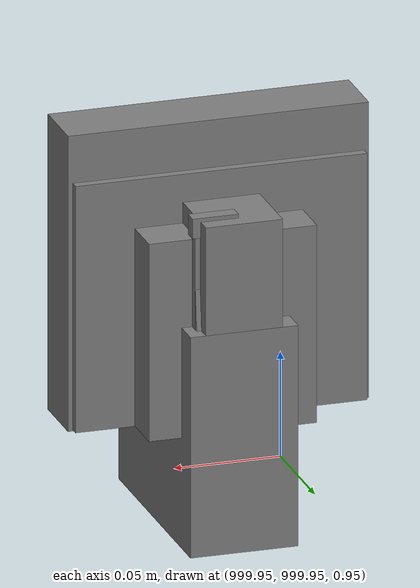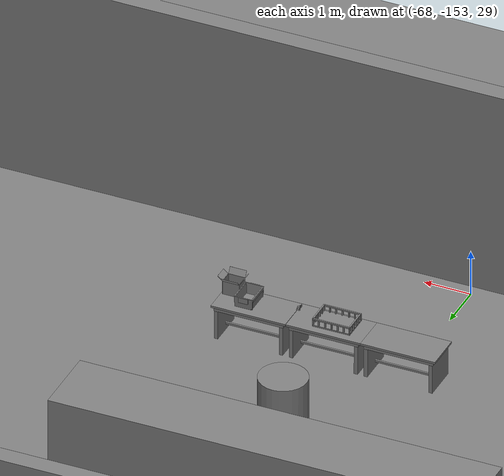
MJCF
<mujoco>
    <option gravity="0.000000000 0.000000000 -9.810000420" timestep="0.0049999999" integrator="implicitfast" density="1.225" viscosity="1.8000001e-05" noslip_iterations="10" iterations="100" sdf_iterations="50">
        <flag multiccd="disable"/>
    </option>
    <size memory="1000M"/>
    <compiler coordinate="local"/>
    <worldbody>
        <light cutoff="30" pos="0 1 1" dir="0 -1 -2"/>
        <light cutoff="30" pos="0 -1 1" dir="0 1 -2"/>
        <body pos="-64.866622925 -149.383972168 30.183746338" euler="89.999984741 89.999946594 0.000000000" name="openloong_gripper_2f85_fix_base_usda_bluebox_01">
            <geom contype="1" conaffinity="1" density="1000" type="box" material="" rgba="0.500000000 0.500000000 0.500000000 1.000000000" solimp="0.899999976 0.949999988 0.001000000" friction="1.000000000 0.005000000 0.000100000" solref="0.020000000 1.000000000" margin="0" condim="3" group="0" pos="0.276580811 0.187225342 0.000068665" quat="0.707106948 0.000077471 0.707106352 0.000077486" size="0.100000001 0.057999998 0.010000000" name="openloong_gripper_2f85_fix_base_usda_geom_89BD1A5C_CCEF_44B3_A3D8_C1E4565E57EF"/>
            <geom contype="1" conaffinity="1" density="1000" type="box" material="" rgba="0.500000000 0.500000000 0.500000000 1.000000000" solimp="0.899999976 0.949999988 0.001000000" friction="1.000000000 0.005000000 0.000100000" solref="0.020000000 1.000000000" margin="0" condim="3" group="0" pos="0.000000000 0.002883911 0.000000000" quat="0.999999881 0.000000000 0.000000000 0.000000000" size="0.254000008 0.003000000 0.172000006" name="openloong_gripper_2f85_fix_base_usda_geom_293AF485_6DCE_4505_83A5_79C6AE94F1F5"/>
            <geom contype="1" conaffinity="1" density="1000" type="box" material="" rgba="0.500000000 0.500000000 0.500000000 1.000000000" solimp="0.899999976 0.949999988 0.001000000" friction="1.000000000 0.005000000 0.000100000" solref="0.020000000 1.000000000" margin="0" condim="3" group="0" pos="0.000000000 0.124874115 0.173484802" quat="0.999796331 0.020176515 -0.000000015 0.000000030" size="0.259999990 0.119999997 0.007000000" name="openloong_gripper_2f85_fix_base_usda_geom_FD7B20F8_47A5_4944_B9DD_229A20FE02C4"/>
            <geom contype="1" conaffinity="1" density="1000" type="box" material="" rgba="0.500000000 0.500000000 0.500000000 1.000000000" solimp="0.899999976 0.949999988 0.001000000" friction="1.000000000 0.005000000 0.000100000" solref="0.020000000 1.000000000" margin="0" condim="3" group="0" pos="0.000000000 0.124874115 -0.173469543" quat="0.999796331 -0.020176545 -0.000000015 0.000000000" size="0.259999990 0.119999997 0.007000000" name="openloong_gripper_2f85_fix_base_usda_geom_7DF0E57E_0AFF_42DC_B527_1459B28451AE"/>
            <geom contype="1" conaffinity="1" density="1000" type="box" material="" rgba="0.500000000 0.500000000 0.500000000 1.000000000" solimp="0.899999976 0.949999988 0.001000000" friction="1.000000000 0.005000000 0.000100000" solref="0.020000000 1.000000000" margin="0" condim="3" group="0" pos="0.000000000 0.214008331 0.188980103" quat="0.999912977 0.013176724 0.000000015 0.000000000" size="0.259999990 0.029999999 0.012500000" name="openloong_gripper_2f85_fix_base_usda_geom_F00C57FE_CC75_4526_9AB0_938C0FA62EDA"/>
            <geom contype="1" conaffinity="1" density="1000" type="box" material="" rgba="0.500000000 0.500000000 0.500000000 1.000000000" solimp="0.899999976 0.949999988 0.001000000" friction="1.000000000 0.005000000 0.000100000" solref="0.020000000 1.000000000" margin="0" condim="3" group="0" pos="-0.258361816 0.125289917 0.001876831" quat="0.702796936 -0.020792112 0.710783124 0.020769298" size="0.189999998 0.119999997 0.009000000" name="openloong_gripper_2f85_fix_base_usda_geom_976EA11F_06E9_47D0_BFA9_F1D686BDBD75"/>
            <geom contype="1" conaffinity="1" density="1000" type="box" material="" rgba="0.500000000 0.500000000 0.500000000 1.000000000" solimp="0.899999976 0.949999988 0.001000000" friction="1.000000000 0.005000000 0.000100000" solref="0.020000000 1.000000000" margin="0" condim="3" group="0" pos="0.000000000 0.214008331 -0.188980103" quat="0.999912977 -0.013176769 0.000000030 0.000000015" size="0.259999990 0.029999999 0.012500000" name="openloong_gripper_2f85_fix_base_usda_geom_47E87FFC_7F39_4A58_8C22_CA47EDF74EF8"/>
            <geom contype="1" conaffinity="1" density="1000" type="box" material="" rgba="0.500000000 0.500000000 0.500000000 1.000000000" solimp="0.899999976 0.949999988 0.001000000" friction="1.000000000 0.005000000 0.000100000" solref="0.020000000 1.000000000" margin="0" condim="3" group="0" pos="-0.276611328 0.187225342 0.000068665" quat="0.707106650 0.000077441 0.707106709 0.000077456" size="0.100000001 0.057999998 0.010000000" name="openloong_gripper_2f85_fix_base_usda_geom_9D9A3B95_9A8C_4485_9F60_28ED76081C48"/>
            <geom contype="1" conaffinity="1" density="1000" type="box" material="" rgba="0.500000000 0.500000000 0.500000000 1.000000000" solimp="0.899999976 0.949999988 0.001000000" friction="1.000000000 0.005000000 0.000100000" solref="0.020000000 1.000000000" margin="0" condim="3" group="0" pos="0.258331299 0.125289917 0.001876831" quat="0.702851415 0.018856421 0.710823774 -0.019329369" size="0.189999998 0.119999997 0.009000000" name="openloong_gripper_2f85_fix_base_usda_geom_1BC59554_E4CA_4594_81C2_A889CD622622"/>
            <freejoint name="openloong_gripper_2f85_fix_base_usda_bluebox_01_joint"/>
            <site size="0.005000000 0.005000000 0.005000000" rgba="0.500000000 0.500000000 0.500000000 1.000000000" pos="0.000000000 0.000000000 0.000000000" quat="0.999961913 0.008726534 0.000000000 0.000000000" group="0" type="sphere" name="openloong_gripper_2f85_fix_base_usda_bluebox_01site"/>
        </body>
        <body pos="-64.496299744 -149.491867065 30.235729218" euler="0.000000000 0.000000000 89.999946594" name="openloong_gripper_2f85_fix_base_usda_cardboardbox_01">
            <geom contype="1" conaffinity="1" density="1000" type="box" material="" rgba="0.500000000 0.500000000 0.500000000 1.000000000" solimp="0.899999976 0.949999988 0.001000000" friction="1.000000000 0.005000000 0.000100000" solref="0.020000000 1.000000000" margin="0" condim="3" group="0" pos="-0.003166199 -0.004086494 0.005052090" quat="1.000000000 0.000000000 0.000000000 0.000000000" size="0.142499998 0.177500010 0.005000000" name="openloong_gripper_2f85_fix_base_usda_geom_8BCE45B6_0756_4188_B1D7_4A5699F8D77E"/>
            <geom contype="1" conaffinity="1" density="1000" type="box" material="" rgba="0.500000000 0.500000000 0.500000000 1.000000000" solimp="0.899999976 0.949999988 0.001000000" friction="1.000000000 0.005000000 0.000100000" solref="0.020000000 1.000000000" margin="0" condim="3" group="0" pos="-0.003166199 0.170316696 0.150570869" quat="1.000000000 0.000000000 0.000000000 0.000000000" size="0.142499998 0.005000000 0.149999991" name="openloong_gripper_2f85_fix_base_usda_geom_32E20BA7_2305_4FEE_A7FF_31374EC1B394"/>
            <geom contype="1" conaffinity="1" density="1000" type="box" material="" rgba="0.500000000 0.500000000 0.500000000 1.000000000" solimp="0.899999976 0.949999988 0.001000000" friction="1.000000000 0.005000000 0.000100000" solref="0.020000000 1.000000000" margin="0" condim="3" group="0" pos="-0.147399902 -0.005307198 0.150570869" quat="1.000000000 0.000000000 0.000000000 0.000000000" size="0.005000000 0.177500010 0.149999991" name="openloong_gripper_2f85_fix_base_usda_geom_357740B7_F381_47AA_AEAE_4DF6B7343345"/>
            <geom contype="1" conaffinity="1" density="1000" type="box" material="" rgba="0.500000000 0.500000000 0.500000000 1.000000000" solimp="0.899999976 0.949999988 0.001000000" friction="1.000000000 0.005000000 0.000100000" solref="0.020000000 1.000000000" margin="0" condim="3" group="0" pos="0.140275955 -0.005307198 0.150570869" quat="1.000000000 0.000000000 0.000000000 0.000000000" size="0.005000000 0.177500010 0.149999991" name="openloong_gripper_2f85_fix_base_usda_geom_5F0B32E1_1EB2_479B_9084_9B4305026933"/>
            <geom contype="1" conaffinity="1" density="1000" type="box" material="" rgba="0.500000000 0.500000000 0.500000000 1.000000000" solimp="0.899999976 0.949999988 0.001000000" friction="1.000000000 0.005000000 0.000100000" solref="0.020000000 1.000000000" margin="0" condim="3" group="0" pos="-0.003166199 -0.181550980 0.150570869" quat="1.000000000 0.000000000 0.000000000 0.000000000" size="0.142499998 0.005000000 0.149999991" name="openloong_gripper_2f85_fix_base_usda_geom_9F586BF0_ADBE_4B30_B6AD_A3611B18D1B7"/>
            <freejoint name="openloong_gripper_2f85_fix_base_usda_cardboardbox_01_joint"/>
            <site size="0.005000000 0.005000000 0.005000000" rgba="0.500000000 0.500000000 0.500000000 1.000000000" pos="0.000000000 0.000000000 0.000000000" quat="0.999961913 0.008726535 0.000000000 0.000000000" group="0" type="sphere" name="openloong_gripper_2f85_fix_base_usda_site_3BF9C880_1577_4ACF_839B_BA67F73B6400"/>
            <body pos="0.139160156 -0.004048347 0.301930904" euler="-179.999954224 49.383502960 179.999954224" name="openloong_gripper_2f85_fix_base_usda_A1_006">
                <geom contype="1" conaffinity="1" density="1000" type="box" material="" rgba="0.500000000 0.500000000 0.500000000 1.000000000" solimp="0.899999976 0.949999988 0.001000000" friction="1.000000000 0.005000000 0.000100000" solref="0.020000000 1.000000000" margin="0" condim="3" group="0" pos="-0.071587563 0.000009537 0.001745224" quat="0.999999881 0.000000000 0.000000000 0.000000000" size="0.071249999 0.179999992 0.002500000" name="openloong_gripper_2f85_fix_base_usda_geom_0C662088_929D_4CFC_BF61_189AB78E4305"/>
                <joint armature="0" stiffness="0.07" damping="0.0099999998" axis="0.000000 1.000000 0.000000" type="hinge" name="openloong_gripper_2f85_fix_base_usda_A1_006"/>
            </body>
            <body pos="-0.145902634 -0.004086494 0.301938057" euler="-180.000000000 -60.000011444 -180.000000000" name="openloong_gripper_2f85_fix_base_usda_A2_006">
                <geom contype="1" conaffinity="1" density="1000" type="box" material="" rgba="0.500000000 0.500000000 0.500000000 1.000000000" solimp="0.899999976 0.949999988 0.001000000" friction="1.000000000 0.005000000 0.000100000" solref="0.020000000 1.000000000" margin="0" condim="3" group="0" pos="0.071268082 0.000009537 0.002717972" quat="0.000002921 0.000000000 -0.000000030 0.999999881" size="0.071249999 0.179999992 0.002500000" name="openloong_gripper_2f85_fix_base_usda_geom_C4A2C737_991D_4C61_8ACC_3A89BA261A7E"/>
                <joint armature="0" stiffness="0.07" damping="0.0099999998" axis="0.000000 1.000000 0.000000" type="hinge" name="openloong_gripper_2f85_fix_base_usda_A2_006"/>
            </body>
            <body pos="-0.003385544 0.175991058 0.301930904" euler="-125.858116150 -0.000004561 0.000002331" name="openloong_gripper_2f85_fix_base_usda_B2_006">
                <geom contype="1" conaffinity="1" density="1000" type="box" material="" rgba="0.500000000 0.500000000 0.500000000 1.000000000" solimp="0.899999976 0.949999988 0.001000000" friction="1.000000000 0.005000000 0.000100000" solref="0.020000000 1.000000000" margin="0" condim="3" group="0" pos="0.000009537 -0.070939064 -0.002470016" quat="0.999614120 0.027776197 -0.000000015 0.000000030" size="0.137500003 0.064999998 0.005000000" name="openloong_gripper_2f85_fix_base_usda_geom_686F2D64_F84E_4729_87BB_B179AB38E4B8"/>
                <joint armature="0" stiffness="0.07" damping="0.0099999998" axis="1.000000 0.000000 0.000000" type="hinge" name="openloong_gripper_2f85_fix_base_usda_B2_006"/>
            </body>
            <body pos="-0.003385544 -0.184140205 0.301938057" euler="147.805557251 0.000000000 0.000000000" name="openloong_gripper_2f85_fix_base_usda_B1_006">
                <geom contype="1" conaffinity="1" density="1000" type="box" material="" rgba="0.500000000 0.500000000 0.500000000 1.000000000" solimp="0.899999976 0.949999988 0.001000000" friction="1.000000000 0.005000000 0.000100000" solref="0.020000000 1.000000000" margin="0" condim="3" group="0" pos="-0.000028610 0.070202351 -0.002703667" quat="0.999614179 -0.027776167 0.000000000 0.000000000" size="0.137500003 0.064999998 0.005000000" name="openloong_gripper_2f85_fix_base_usda_geom_2F179B17_1039_4158_86DA_F1671D0B5CC7"/>
                <joint armature="0" stiffness="0.07" damping="0.0099999998" axis="1.000000 0.000000 0.000000" type="hinge" name="openloong_gripper_2f85_fix_base_usda_B1_006"/>
            </body>
        </body>
        <body pos="-65.882858276 -149.481979370 30.229999542" euler="-64.487716675 0.000000000 0.000000000" name="openloong_gripper_2f85_fix_base_usda_Barcode">
            <geom contype="1" conaffinity="1" density="1000" type="box" material="" rgba="0.500000000 0.500000000 0.500000000 1.000000000" solimp="0.899999976 0.949999988 0.001000000" friction="1.000000000 0.005000000 0.000100000" solref="0.020000000 1.000000000" margin="0" condim="3" group="0" pos="0.000000000 0.013038635 0.001419067" quat="0.000000000 0.000000000 0.000000000 1.000000119" size="0.034000002 0.010000000 0.017999999" name="openloong_gripper_2f85_fix_base_usda_geom_F7CB8FCA_B572_4CBB_AD37_41CD9E54F7CB"/>
            <geom contype="1" conaffinity="1" density="1000" type="box" material="" rgba="0.500000000 0.500000000 0.500000000 1.000000000" solimp="0.899999976 0.949999988 0.001000000" friction="1.000000000 0.005000000 0.000100000" solref="0.020000000 1.000000000" margin="0" condim="3" group="0" pos="0.000000000 -0.035301208 -0.007095337" quat="0.000000000 0.000000000 -0.043619365 0.999048233" size="0.028999999 0.010000000 0.020000000" name="openloong_gripper_2f85_fix_base_usda_geom_24B0AB4C_A774_4CA8_95DB_9C8AA598B54F"/>
            <geom contype="1" conaffinity="1" density="1000" type="box" material="" rgba="0.500000000 0.500000000 0.500000000 1.000000000" solimp="0.899999976 0.949999988 0.001000000" friction="1.000000000 0.005000000 0.000100000" solref="0.020000000 1.000000000" margin="0" condim="3" group="0" pos="0.000000000 -0.043411255 -0.011749268" quat="0.922262907 0.386563420 0.000000000 0.000000000" size="0.026000001 0.010000000 0.020000000" name="openloong_gripper_2f85_fix_base_usda_geom_57F931E6_16E8_4B2B_B6EC_54D169ED0A62"/>
            <geom contype="1" conaffinity="1" density="1000" type="box" material="" rgba="0.500000000 0.500000000 0.500000000 1.000000000" solimp="0.899999976 0.949999988 0.001000000" friction="1.000000000 0.005000000 0.000100000" solref="0.020000000 1.000000000" margin="0" condim="3" group="0" pos="0.000000000 -0.016967773 -0.031860352" quat="0.000000000 0.000000000 0.000000000 1.000000119" size="0.008000000 0.010000000 0.013000000" name="openloong_gripper_2f85_fix_base_usda_geom_1B983D1B_CEE0_464D_8E05_5056CFD1AD18"/>
            <geom contype="1" conaffinity="1" density="1000" type="box" material="" rgba="0.500000000 0.500000000 0.500000000 1.000000000" solimp="0.899999976 0.949999988 0.001000000" friction="1.000000000 0.005000000 0.000100000" solref="0.020000000 1.000000000" margin="0" condim="3" group="0" pos="0.000000000 -0.001869202 0.000312805" quat="0.953716993 0.300705761 0.000000000 0.000000000" size="0.032000002 0.010000000 0.018999999" name="openloong_gripper_2f85_fix_base_usda_geom_68F18189_407F_4592_A4BE_47C105F03955"/>
            <geom contype="1" conaffinity="1" density="1000" type="box" material="" rgba="0.500000000 0.500000000 0.500000000 1.000000000" solimp="0.899999976 0.949999988 0.001000000" friction="1.000000000 0.005000000 0.000100000" solref="0.020000000 1.000000000" margin="0" condim="3" group="0" pos="0.000000000 -0.019531250 -0.003173828" quat="0.953716993 0.300705761 0.000000000 0.000000000" size="0.030999999 0.010000000 0.020000000" name="openloong_gripper_2f85_fix_base_usda_geom_A60E9D25_6C41_4CAE_AA32_3DC96ED8DDC6"/>
            <geom contype="1" conaffinity="1" density="1000" type="box" material="" rgba="0.500000000 0.500000000 0.500000000 1.000000000" solimp="0.899999976 0.949999988 0.001000000" friction="1.000000000 0.005000000 0.000100000" solref="0.020000000 1.000000000" margin="0" condim="3" group="0" pos="0.000000000 -0.035301208 -0.007095337" quat="0.953716993 0.300705761 0.000000000 0.000000000" size="0.028999999 0.010000000 0.020000000" name="openloong_gripper_2f85_fix_base_usda_geom_2AE2AA14_A900_4DDE_B39E_EB7F673BB05A"/>
            <geom contype="1" conaffinity="1" density="1000" type="box" material="" rgba="0.500000000 0.500000000 0.500000000 1.000000000" solimp="0.899999976 0.949999988 0.001000000" friction="1.000000000 0.005000000 0.000100000" solref="0.020000000 1.000000000" margin="0" condim="3" group="0" pos="0.000000000 -0.042617798 -0.071121216" quat="0.000000000 0.000000000 0.000000000 1.000000119" size="0.013000000 0.021000000 0.059999999" name="openloong_gripper_2f85_fix_base_usda_geom_081766D1_A994_44BF_8EBC_1895A43BAFD8"/>
            <freejoint name="openloong_gripper_2f85_fix_base_usda_Barcode_joint"/>
            <site size="0.005000000 0.005000000 0.005000000" rgba="0.500000000 0.500000000 0.500000000 1.000000000" pos="0.000000000 0.000000000 0.000000000" quat="1.000000000 0.000000000 0.000000000 0.000000000" group="0" type="sphere" name="openloong_gripper_2f85_fix_base_usda_Barcode_site"/>
        </body>
        <body pos="-66.745018005 -149.392349243 30.184000015" euler="0.000000000 0.000000000 89.999946594" name="[22333193934198]_Basket_01">
            <geom contype="1" conaffinity="1" density="1000" type="box" material="" rgba="0.500000000 0.500000000 0.500000000 1.000000000" solimp="0.899999976 0.949999988 0.001000000" friction="1.000000000 0.005000000 0.000100000" solref="0.020000000 1.000000000" margin="0" condim="3" group="0" pos="-0.052425385 0.389207840 0.089787483" quat="0.707107008 0.000000000 0.000000000 0.707106411" size="0.014249999 0.014249999 0.059999999" name="[22333193934198]_geom_8FCF0400_851E_44A7_809D_0C2B518FF8D7"/>
            <geom contype="1" conaffinity="1" density="1000" type="box" material="" rgba="0.500000000 0.500000000 0.500000000 1.000000000" solimp="0.899999976 0.949999988 0.001000000" friction="1.000000000 0.005000000 0.000100000" solref="0.020000000 1.000000000" margin="0" condim="3" group="0" pos="0.264015198 -0.133043289 0.089787483" quat="0.707107008 0.000000000 0.000000000 0.707106411" size="0.014249999 0.014249999 0.059999999" name="[22333193934198]_geom_5CC7F7FB_9BFB_482A_93D9_B23790B0CBBD"/>
            <geom contype="1" conaffinity="1" density="1000" type="box" material="" rgba="0.500000000 0.500000000 0.500000000 1.000000000" solimp="0.899999976 0.949999988 0.001000000" friction="1.000000000 0.005000000 0.000100000" solref="0.020000000 1.000000000" margin="0" condim="3" group="0" pos="-0.264015198 -0.265548706 0.089793205" quat="0.707107008 0.000000000 0.000000000 0.707106411" size="0.014249999 0.014249999 0.059999999" name="[22333193934198]_geom_641172D5_282B_4C0F_A03F_D4685CF5C43B"/>
            <geom contype="1" conaffinity="1" density="1000" type="box" material="" rgba="0.500000000 0.500000000 0.500000000 1.000000000" solimp="0.899999976 0.949999988 0.001000000" friction="1.000000000 0.005000000 0.000100000" solref="0.020000000 1.000000000" margin="0" condim="3" group="0" pos="-0.160263062 -0.389322281 0.089793205" quat="0.707107008 0.000000000 0.000000000 0.707106411" size="0.014249999 0.014249999 0.059999999" name="[22333193934198]_geom_5765590A_680D_450D_85D9_D08040F11462"/>
            <geom contype="1" conaffinity="1" density="1000" type="box" material="" rgba="0.500000000 0.500000000 0.500000000 1.000000000" solimp="0.899999976 0.949999988 0.001000000" friction="1.000000000 0.005000000 0.000100000" solref="0.020000000 1.000000000" margin="0" condim="3" group="0" pos="0.162265778 -0.389322281 0.089787483" quat="0.707107008 0.000000000 0.000000000 0.707106411" size="0.014249999 0.014249999 0.059999999" name="[22333193934198]_geom_6C9CA063_D6B7_4B96_AE5D_FBCAD0ED5B6F"/>
            <geom contype="1" conaffinity="1" density="1000" type="box" material="" rgba="0.500000000 0.500000000 0.500000000 1.000000000" solimp="0.899999976 0.949999988 0.001000000" friction="1.000000000 0.005000000 0.000100000" solref="0.020000000 1.000000000" margin="0" condim="3" group="0" pos="0.264015198 0.389207840 0.089787483" quat="0.707107008 0.000000000 0.000000000 0.707106411" size="0.014249999 0.014249999 0.059999999" name="[22333193934198]_geom_D47EEC43_101A_4D67_B100_9D6663CBC669"/>
            <geom contype="1" conaffinity="1" density="1000" type="box" material="" rgba="0.500000000 0.500000000 0.500000000 1.000000000" solimp="0.899999976 0.949999988 0.001000000" friction="1.000000000 0.005000000 0.000100000" solref="0.020000000 1.000000000" margin="0" condim="3" group="0" pos="-0.264015198 -0.133043289 0.089793205" quat="0.707107008 0.000000000 0.000000000 0.707106411" size="0.014249999 0.014249999 0.059999999" name="[22333193934198]_geom_36BB37D7_730E_47CE_9F96_5E16A567DE97"/>
            <geom contype="1" conaffinity="1" density="1000" type="box" material="" rgba="0.500000000 0.500000000 0.500000000 1.000000000" solimp="0.899999976 0.949999988 0.001000000" friction="1.000000000 0.005000000 0.000100000" solref="0.020000000 1.000000000" margin="0" condim="3" group="0" pos="-0.264026642 0.269256592 0.089793205" quat="0.707107008 0.000000000 0.000000000 0.707106411" size="0.014249999 0.014249999 0.059999999" name="[22333193934198]_geom_1C6223A6_A3E5_41C2_8637_2D7F4640E5BE"/>
            <geom contype="1" conaffinity="1" density="1000" type="box" material="" rgba="0.500000000 0.500000000 0.500000000 1.000000000" solimp="0.899999976 0.949999988 0.001000000" friction="1.000000000 0.005000000 0.000100000" solref="0.020000000 1.000000000" margin="0" condim="3" group="0" pos="0.054462433 0.389207840 0.089787483" quat="0.707107008 0.000000000 0.000000000 0.707106411" size="0.014249999 0.014249999 0.059999999" name="[22333193934198]_geom_4FD951ED_CE22_424A_9648_FA566E563639"/>
            <geom contype="1" conaffinity="1" density="1000" type="box" material="" rgba="0.500000000 0.500000000 0.500000000 1.000000000" solimp="0.899999976 0.949999988 0.001000000" friction="1.000000000 0.005000000 0.000100000" solref="0.020000000 1.000000000" margin="0" condim="3" group="0" pos="0.054462433 -0.389322281 0.089787483" quat="0.707107008 0.000000000 0.000000000 0.707106411" size="0.014249999 0.014249999 0.059999999" name="[22333193934198]_geom_A587654C_B29A_41C4_B39A_9A47A112FFC3"/>
            <geom contype="1" conaffinity="1" density="1000" type="box" material="" rgba="0.500000000 0.500000000 0.500000000 1.000000000" solimp="0.899999976 0.949999988 0.001000000" friction="1.000000000 0.005000000 0.000100000" solref="0.020000000 1.000000000" margin="0" condim="3" group="0" pos="0.264015198 0.269256592 0.089793205" quat="0.707107008 0.000000000 0.000000000 0.707106411" size="0.014249999 0.014249999 0.059999999" name="[22333193934198]_geom_EBDC99FF_3BBF_471E_8EF1_03956C0B08D3"/>
            <geom contype="1" conaffinity="1" density="1000" type="box" material="" rgba="0.500000000 0.500000000 0.500000000 1.000000000" solimp="0.899999976 0.949999988 0.001000000" friction="1.000000000 0.005000000 0.000100000" solref="0.020000000 1.000000000" margin="0" condim="3" group="0" pos="0.264015198 -0.389322281 0.089787483" quat="0.707107008 0.000000000 0.000000000 0.707106411" size="0.014249999 0.014249999 0.059999999" name="[22333193934198]_geom_8492233E_872D_4FA0_B8A0_5ACE44092AE4"/>
            <geom contype="1" conaffinity="1" density="1000" type="box" material="" rgba="0.500000000 0.500000000 0.500000000 1.000000000" solimp="0.899999976 0.949999988 0.001000000" friction="1.000000000 0.005000000 0.000100000" solref="0.020000000 1.000000000" margin="0" condim="3" group="0" pos="0.000000000 0.000000000 0.015998840" quat="0.707107008 0.000000000 0.000000000 0.707106411" size="0.403499991 0.279000014 0.015750000" name="[22333193934198]_geom_10EE46DB_CF36_48EF_B0AE_A4218BA07BE4"/>
            <geom contype="1" conaffinity="1" density="1000" type="box" material="" rgba="0.500000000 0.500000000 0.500000000 1.000000000" solimp="0.899999976 0.949999988 0.001000000" friction="1.000000000 0.005000000 0.000100000" solref="0.020000000 1.000000000" margin="0" condim="3" group="0" pos="0.000000000 -0.389476776 0.163619041" quat="0.707107008 0.000000000 0.000000000 0.707106411" size="0.015000000 0.277500004 0.015750000" name="[22333193934198]_geom_852A6491_2ED6_486E_9AC1_1B3C8E812362"/>
            <geom contype="1" conaffinity="1" density="1000" type="box" material="" rgba="0.500000000 0.500000000 0.500000000 1.000000000" solimp="0.899999976 0.949999988 0.001000000" friction="1.000000000 0.005000000 0.000100000" solref="0.020000000 1.000000000" margin="0" condim="3" group="0" pos="0.162265778 0.389207840 0.089787483" quat="0.707107008 0.000000000 0.000000000 0.707106411" size="0.014249999 0.014249999 0.059999999" name="[22333193934198]_geom_2D5F4BCD_8F52_405D_9E07_6B978C2B17F7"/>
            <geom contype="1" conaffinity="1" density="1000" type="box" material="" rgba="0.500000000 0.500000000 0.500000000 1.000000000" solimp="0.899999976 0.949999988 0.001000000" friction="1.000000000 0.005000000 0.000100000" solref="0.020000000 1.000000000" margin="0" condim="3" group="0" pos="0.000000000 0.389471054 0.163619041" quat="0.707107008 0.000000000 0.000000000 0.707106411" size="0.015000000 0.277500004 0.015750000" name="[22333193934198]_geom_FF158C91_D03B_4526_BD2D_134D32207ECC"/>
            <geom contype="1" conaffinity="1" density="1000" type="box" material="" rgba="0.500000000 0.500000000 0.500000000 1.000000000" solimp="0.899999976 0.949999988 0.001000000" friction="1.000000000 0.005000000 0.000100000" solref="0.020000000 1.000000000" margin="0" condim="3" group="0" pos="-0.263511658 0.000000000 0.163619041" quat="0.707107008 0.000000000 0.000000000 0.707106411" size="0.403499991 0.015000000 0.015750000" name="[22333193934198]_geom_0E4FF3D2_EA2A_4C8A_80CF_2550FE39B12E"/>
            <geom contype="1" conaffinity="1" density="1000" type="box" material="" rgba="0.500000000 0.500000000 0.500000000 1.000000000" solimp="0.899999976 0.949999988 0.001000000" friction="1.000000000 0.005000000 0.000100000" solref="0.020000000 1.000000000" margin="0" condim="3" group="0" pos="-0.264015198 0.141334534 0.089793205" quat="0.707107008 0.000000000 0.000000000 0.707106411" size="0.014249999 0.014249999 0.059999999" name="[22333193934198]_geom_A1F04675_7D86_4BD3_8BD2_F7913A84B8D0"/>
            <geom contype="1" conaffinity="1" density="1000" type="box" material="" rgba="0.500000000 0.500000000 0.500000000 1.000000000" solimp="0.899999976 0.949999988 0.001000000" friction="1.000000000 0.005000000 0.000100000" solref="0.020000000 1.000000000" margin="0" condim="3" group="0" pos="0.264015198 -0.265548706 0.089787483" quat="0.707107008 0.000000000 0.000000000 0.707106411" size="0.014249999 0.014249999 0.059999999" name="[22333193934198]_geom_9B4131BC_E6BA_466C_A0A6_13043D152CB2"/>
            <geom contype="1" conaffinity="1" density="1000" type="box" material="" rgba="0.500000000 0.500000000 0.500000000 1.000000000" solimp="0.899999976 0.949999988 0.001000000" friction="1.000000000 0.005000000 0.000100000" solref="0.020000000 1.000000000" margin="0" condim="3" group="0" pos="-0.160263062 0.389207840 0.089787483" quat="0.707107008 0.000000000 0.000000000 0.707106411" size="0.014249999 0.014249999 0.059999999" name="[22333193934198]_geom_E85F4716_5FA8_4A5F_B807_3F7951624127"/>
            <geom contype="1" conaffinity="1" density="1000" type="box" material="" rgba="0.500000000 0.500000000 0.500000000 1.000000000" solimp="0.899999976 0.949999988 0.001000000" friction="1.000000000 0.005000000 0.000100000" solref="0.020000000 1.000000000" margin="0" condim="3" group="0" pos="-0.052425385 -0.389322281 0.089787483" quat="0.707107008 0.000000000 0.000000000 0.707106411" size="0.014249999 0.014249999 0.059999999" name="[22333193934198]_geom_93111C46_1BF0_4E4B_8E0B_3FF784785AF0"/>
            <geom contype="1" conaffinity="1" density="1000" type="box" material="" rgba="0.500000000 0.500000000 0.500000000 1.000000000" solimp="0.899999976 0.949999988 0.001000000" friction="1.000000000 0.005000000 0.000100000" solref="0.020000000 1.000000000" margin="0" condim="3" group="0" pos="-0.264026642 -0.389322281 0.089793205" quat="0.707107008 0.000000000 0.000000000 0.707106411" size="0.014249999 0.014249999 0.059999999" name="[22333193934198]_geom_2550BECD_02B3_4687_B5BA_F9D58E951EDB"/>
            <geom contype="1" conaffinity="1" density="1000" type="box" material="" rgba="0.500000000 0.500000000 0.500000000 1.000000000" solimp="0.899999976 0.949999988 0.001000000" friction="1.000000000 0.005000000 0.000100000" solref="0.020000000 1.000000000" margin="0" condim="3" group="0" pos="0.264015198 0.141334534 0.089787483" quat="0.707107008 0.000000000 0.000000000 0.707106411" size="0.014249999 0.014249999 0.059999999" name="[22333193934198]_geom_B244721F_5A9D_4599_884F_20798F4B465F"/>
            <geom contype="1" conaffinity="1" density="1000" type="box" material="" rgba="0.500000000 0.500000000 0.500000000 1.000000000" solimp="0.899999976 0.949999988 0.001000000" friction="1.000000000 0.005000000 0.000100000" solref="0.020000000 1.000000000" margin="0" condim="3" group="0" pos="-0.264015198 0.389207840 0.089793205" quat="0.707107008 0.000000000 0.000000000 0.707106411" size="0.014249999 0.014249999 0.059999999" name="[22333193934198]_geom_FBE90135_0762_407D_9E40_96D7A980C377"/>
            <geom contype="1" conaffinity="1" density="1000" type="box" material="" rgba="0.500000000 0.500000000 0.500000000 1.000000000" solimp="0.899999976 0.949999988 0.001000000" friction="1.000000000 0.005000000 0.000100000" solref="0.020000000 1.000000000" margin="0" condim="3" group="0" pos="0.264015198 0.004480362 0.089787483" quat="0.707107008 0.000000000 0.000000000 0.707106411" size="0.014249999 0.014249999 0.059999999" name="[22333193934198]_geom_F5C4E8B3_44B0_41FA_94D2_1687A62F81E1"/>
            <geom contype="1" conaffinity="1" density="1000" type="box" material="" rgba="0.500000000 0.500000000 0.500000000 1.000000000" solimp="0.899999976 0.949999988 0.001000000" friction="1.000000000 0.005000000 0.000100000" solref="0.020000000 1.000000000" margin="0" condim="3" group="0" pos="0.263694763 -0.000011444 0.163619041" quat="0.707107008 0.000000000 0.000000000 0.707106411" size="0.403499991 0.015000000 0.015750000" name="[22333193934198]_geom_5546B652_5FD4_49D1_945C_9DCB7140BA4A"/>
            <geom contype="1" conaffinity="1" density="1000" type="box" material="" rgba="0.500000000 0.500000000 0.500000000 1.000000000" solimp="0.899999976 0.949999988 0.001000000" friction="1.000000000 0.005000000 0.000100000" solref="0.020000000 1.000000000" margin="0" condim="3" group="0" pos="-0.264015198 0.004480362 0.089793205" quat="0.707107008 0.000000000 0.000000000 0.707106411" size="0.014249999 0.014249999 0.059999999" name="[22333193934198]_geom_2C54AEB4_8867_4B54_9800_F8AC7E1764EF"/>
            <freejoint name="[22333193934198]_joint_B8C8EF90_CE12_41B3_9C33_EB5158EA71F2"/>
        </body>
        <body pos="0.000000000 0.000000000 0.000000000" euler="0.000000000 0.000000000 0.000000000" name="Static Objects_Static Objects">
            <geom contype="1" conaffinity="1" density="1000" type="box" material="" rgba="0.500000000 0.500000000 0.500000000 1.000000000" solimp="0.899999976 0.949999988 0.001000000" friction="1.000000000 0.005000000 0.000100000" solref="0.020000000 1.000000000" margin="0" condim="3" group="0" pos="-67.544113159 -149.365814209 29.727830887" quat="0.500000417 0.499999970 0.499999553 0.499999970" size="0.381000012 0.319999993 0.041000001" name="Static Objects_geom_E081F6A2_CBC5_4931_866A_5CF11583166E"/>
            <geom contype="1" conaffinity="1" density="1000" type="box" material="" rgba="0.500000000 0.500000000 0.500000000 1.000000000" solimp="0.899999976 0.949999988 0.001000000" friction="1.000000000 0.005000000 0.000100000" solref="0.020000000 1.000000000" margin="0" condim="3" group="0" pos="-68.239501953 -149.365814209 30.086868286" quat="0.500000417 0.499999970 0.499999553 0.499999970" size="0.370999992 0.039500002 0.745000005" name="Static Objects_geom_00DD40BD_4321_4100_8BEB_81F756A2EFD9"/>
            <geom contype="1" conaffinity="1" density="1000" type="box" material="" rgba="0.500000000 0.500000000 0.500000000 1.000000000" solimp="0.899999976 0.949999988 0.001000000" friction="1.000000000 0.005000000 0.000100000" solref="0.020000000 1.000000000" margin="0" condim="3" group="0" pos="-68.239501953 -149.365814209 30.147235870" quat="0.500000417 0.499999970 0.499999553 0.499999970" size="0.400000006 0.022000000 0.800000012" name="Static Objects_geom_CC07FD9B_1324_4AEE_A9CD_9F5B513D34E8"/>
            <geom contype="1" conaffinity="1" density="1000" type="box" material="" rgba="0.500000000 0.500000000 0.500000000 1.000000000" solimp="0.899999976 0.949999988 0.001000000" friction="1.000000000 0.005000000 0.000100000" solref="0.020000000 1.000000000" margin="0" condim="3" group="0" pos="-68.934890747 -149.365814209 29.727830887" quat="0.500000417 0.499999970 0.499999553 0.499999970" size="0.381000012 0.319999993 0.041000001" name="Static Objects_geom_36DE712B_04ED_4A5A_9893_1C772A69238A"/>
            <geom contype="1" conaffinity="1" density="1000" type="box" material="" rgba="0.500000000 0.500000000 0.500000000 1.000000000" solimp="0.899999976 0.949999988 0.001000000" friction="1.000000000 0.005000000 0.000100000" solref="0.020000000 1.000000000" margin="0" condim="3" group="0" pos="-68.239501953 -149.365814209 29.561563492" quat="0.500000417 0.499999970 0.499999553 0.499999970" size="0.020000000 0.022000000 0.660000026" name="Static Objects_geom_BADFE2E8_BE4A_4ED4_9AD7_EDD5C218304D"/>
            <geom contype="1" conaffinity="1" density="1000" type="box" material="" rgba="0.500000000 0.500000000 0.500000000 1.000000000" solimp="0.899999976 0.949999988 0.001000000" friction="1.000000000 0.005000000 0.000100000" solref="0.020000000 1.000000000" margin="0" condim="3" group="0" pos="-65.945671082 -149.365814209 29.727830887" quat="0.500000417 0.499999970 0.499999553 0.499999970" size="0.381000012 0.319999993 0.041000001" name="Static Objects_geom_D83FCBB1_895C_46B9_B7C7_E52BC872BE76"/>
            <geom contype="1" conaffinity="1" density="1000" type="box" material="" rgba="0.500000000 0.500000000 0.500000000 1.000000000" solimp="0.899999976 0.949999988 0.001000000" friction="1.000000000 0.005000000 0.000100000" solref="0.020000000 1.000000000" margin="0" condim="3" group="0" pos="-66.641059875 -149.365814209 30.086868286" quat="0.500000417 0.499999970 0.499999553 0.499999970" size="0.370999992 0.039500002 0.745000005" name="Static Objects_geom_1A9EC7EA_8D33_4CE5_B6BE_29777198F111"/>
            <geom contype="1" conaffinity="1" density="1000" type="box" material="" rgba="0.500000000 0.500000000 0.500000000 1.000000000" solimp="0.899999976 0.949999988 0.001000000" friction="1.000000000 0.005000000 0.000100000" solref="0.020000000 1.000000000" margin="0" condim="3" group="0" pos="-66.641059875 -149.365814209 30.147235870" quat="0.500000417 0.499999970 0.499999553 0.499999970" size="0.400000006 0.022000000 0.800000012" name="Static Objects_geom_CB3B0765_54FA_4A92_9BC6_28046E385012"/>
            <geom contype="1" conaffinity="1" density="1000" type="box" material="" rgba="0.500000000 0.500000000 0.500000000 1.000000000" solimp="0.899999976 0.949999988 0.001000000" friction="1.000000000 0.005000000 0.000100000" solref="0.020000000 1.000000000" margin="0" condim="3" group="0" pos="-67.336448669 -149.365814209 29.727830887" quat="0.500000417 0.499999970 0.499999553 0.499999970" size="0.381000012 0.319999993 0.041000001" name="Static Objects_geom_3FFCA1BC_6FA4_4DF8_8327_86BE21EA5B7A"/>
            <geom contype="1" conaffinity="1" density="1000" type="box" material="" rgba="0.500000000 0.500000000 0.500000000 1.000000000" solimp="0.899999976 0.949999988 0.001000000" friction="1.000000000 0.005000000 0.000100000" solref="0.020000000 1.000000000" margin="0" condim="3" group="0" pos="-66.641059875 -149.365814209 29.561563492" quat="0.500000417 0.499999970 0.499999553 0.499999970" size="0.020000000 0.022000000 0.660000026" name="Static Objects_geom_F7111563_9812_49C2_8D8A_88E526D3A842"/>
            <geom contype="1" conaffinity="1" density="1000" type="box" material="" rgba="0.500000000 0.500000000 0.500000000 1.000000000" solimp="0.899999976 0.949999988 0.001000000" friction="1.000000000 0.005000000 0.000100000" solref="0.020000000 1.000000000" margin="0" condim="3" group="0" pos="-64.338577271 -149.365814209 29.727830887" quat="0.500000417 0.499999970 0.499999553 0.499999970" size="0.381000012 0.319999993 0.041000001" name="Static Objects_geom_ABDE444B_34E6_4818_B5F6_A2FE16344167"/>
            <geom contype="1" conaffinity="1" density="1000" type="box" material="" rgba="0.500000000 0.500000000 0.500000000 1.000000000" solimp="0.899999976 0.949999988 0.001000000" friction="1.000000000 0.005000000 0.000100000" solref="0.020000000 1.000000000" margin="0" condim="3" group="0" pos="-65.033966064 -149.365814209 30.086868286" quat="0.500000417 0.499999970 0.499999553 0.499999970" size="0.370999992 0.039500002 0.745000005" name="Static Objects_geom_0622BBE8_B20E_4C6C_B0BB_DEA328C3CE50"/>
            <geom contype="1" conaffinity="1" density="1000" type="box" material="" rgba="0.500000000 0.500000000 0.500000000 1.000000000" solimp="0.899999976 0.949999988 0.001000000" friction="1.000000000 0.005000000 0.000100000" solref="0.020000000 1.000000000" margin="0" condim="3" group="0" pos="-65.033966064 -149.365814209 30.147235870" quat="0.500000417 0.499999970 0.499999553 0.499999970" size="0.400000006 0.022000000 0.800000012" name="Static Objects_geom_CE1522DE_719E_4C5C_8D0F_C4CC97D27BF6"/>
            <geom contype="1" conaffinity="1" density="1000" type="box" material="" rgba="0.500000000 0.500000000 0.500000000 1.000000000" solimp="0.899999976 0.949999988 0.001000000" friction="1.000000000 0.005000000 0.000100000" solref="0.020000000 1.000000000" margin="0" condim="3" group="0" pos="-65.729354858 -149.365814209 29.727830887" quat="0.500000417 0.499999970 0.499999553 0.499999970" size="0.381000012 0.319999993 0.041000001" name="Static Objects_geom_8E0F057F_2E5F_4E69_B531_5055ADA53FCA"/>
            <geom contype="1" conaffinity="1" density="1000" type="box" material="" rgba="0.500000000 0.500000000 0.500000000 1.000000000" solimp="0.899999976 0.949999988 0.001000000" friction="1.000000000 0.005000000 0.000100000" solref="0.020000000 1.000000000" margin="0" condim="3" group="0" pos="-65.033966064 -149.365814209 29.561563492" quat="0.500000417 0.499999970 0.499999553 0.499999970" size="0.020000000 0.022000000 0.660000026" name="Static Objects_geom_985997B3_A1AB_413A_AE0F_4DA8F52688F5"/>
            <geom contype="1" conaffinity="1" density="1000" type="box" material="" rgba="0.500000000 0.500000000 0.500000000 1.000000000" solimp="0.899999976 0.949999988 0.001000000" friction="1.000000000 0.005000000 0.000100000" solref="0.020000000 1.000000000" margin="0" condim="3" group="0" pos="-61.754566193 -137.853729248 33.906845093" quat="0.707107067 0.000000000 0.000000000 0.707106471" size="0.759999990 0.759999990 4.500000000" name="Static Objects_geom_DD8B1E82_B05E_42AF_B78D_DE73D41C6F1C"/>
            <geom contype="1" conaffinity="1" density="1000" type="box" material="" rgba="0.500000000 0.500000000 0.500000000 1.000000000" solimp="0.899999976 0.949999988 0.001000000" friction="1.000000000 0.005000000 0.000100000" solref="0.020000000 1.000000000" margin="0" condim="3" group="0" pos="-57.511135101 -144.927108765 31.707921982" quat="1.000000000 0.000000000 0.000000000 0.000000000" size="0.200000003 8.000000000 2.299999952" name="Static Objects_geom_3F6D413C_DEE3_47C2_BE99_70898B12A512"/>
            <geom contype="1" conaffinity="1" density="1000" type="box" material="" rgba="0.500000000 0.500000000 0.500000000 1.000000000" solimp="0.899999976 0.949999988 0.001000000" friction="1.000000000 0.005000000 0.000100000" solref="0.020000000 1.000000000" margin="0" condim="3" group="0" pos="-80.517646790 -157.574050903 31.688196182" quat="0.707107067 0.000000000 0.000000000 0.707106471" size="0.600000024 0.600000024 2.299999952" name="Static Objects_geom_C56DB392_2107_4FA0_8829_EF656E19B7CF"/>
            <geom contype="1" conaffinity="1" density="1000" type="box" material="" rgba="0.500000000 0.500000000 0.500000000 1.000000000" solimp="0.899999976 0.949999988 0.001000000" friction="1.000000000 0.005000000 0.000100000" solref="0.020000000 1.000000000" margin="0" condim="3" group="0" pos="-80.711044312 -147.414932251 31.666158676" quat="1.000000000 0.000000000 0.000000000 0.000000000" size="0.200000003 10.000000000 2.299999952" name="Static Objects_geom_9B706025_3204_4F10_8CB0_56CA5CF12F34"/>
            <geom contype="1" conaffinity="1" density="1000" type="box" material="" rgba="0.500000000 0.500000000 0.500000000 1.000000000" solimp="0.899999976 0.949999988 0.001000000" friction="1.000000000 0.005000000 0.000100000" solref="0.020000000 1.000000000" margin="0" condim="3" group="0" pos="-57.687217712 -137.434692383 31.688196182" quat="0.707107067 0.000000000 0.000000000 0.707106471" size="0.600000024 0.600000024 2.299999952" name="Static Objects_geom_E8E16B47_A950_481E_8A0C_CEAB69E51484"/>
            <geom contype="1" conaffinity="1" density="1000" type="box" material="" rgba="0.500000000 0.500000000 0.500000000 1.000000000" solimp="0.899999976 0.949999988 0.001000000" friction="1.000000000 0.005000000 0.000100000" solref="0.020000000 1.000000000" margin="0" condim="3" group="0" pos="-69.537033081 -140.263229370 31.714921951" quat="0.707107067 0.000000000 0.000000000 0.707106471" size="0.759999990 4.500000000 2.299999952" name="Static Objects_geom_6C4AC287_AA2C_42E4_9B90_AEE5594A238C"/>
            <geom contype="1" conaffinity="1" density="1000" type="box" material="" rgba="0.500000000 0.500000000 0.500000000 1.000000000" solimp="0.899999976 0.949999988 0.001000000" friction="1.000000000 0.005000000 0.000100000" solref="0.020000000 1.000000000" margin="0" condim="3" group="0" pos="-80.073638916 -137.853713989 33.906845093" quat="0.707107067 0.000000000 0.000000000 0.707106471" size="0.759999990 0.759999990 4.500000000" name="Static Objects_geom_7A3764DC_5C04_4BCA_96E2_3D52570C599C"/>
            <geom contype="1" conaffinity="1" density="1000" type="box" material="" rgba="0.500000000 0.500000000 0.500000000 1.000000000" solimp="0.899999976 0.949999988 0.001000000" friction="1.000000000 0.005000000 0.000100000" solref="0.020000000 1.000000000" margin="0" condim="3" group="0" pos="-73.406707764 -155.734664917 31.707921982" quat="1.000000000 0.000000000 0.000000000 0.000000000" size="0.200000003 3.000000000 2.299999952" name="Static Objects_geom_7D316679_5A5B_4E9A_B279_0E9617278D77"/>
            <geom contype="1" conaffinity="1" density="1000" type="box" material="" rgba="0.500000000 0.500000000 0.500000000 1.000000000" solimp="0.899999976 0.949999988 0.001000000" friction="1.000000000 0.005000000 0.000100000" solref="0.020000000 1.000000000" margin="0" condim="3" group="0" pos="-68.497543335 -137.448257446 31.707921982" quat="0.707107067 0.000000000 0.000000000 0.707106471" size="0.200000003 14.000000000 2.299999952" name="Static Objects_geom_DFF15E72_2653_4844_A798_80DB51AB2870"/>
            <geom contype="1" conaffinity="1" density="1000" type="cylinder" material="" rgba="0.500000000 0.500000000 0.500000000 1.000000000" solimp="0.899999976 0.949999988 0.001000000" friction="1.000000000 0.005000000 0.000100000" solref="0.020000000 1.000000000" margin="0" condim="3" group="0" pos="-68.868522644 -142.134506226 31.711090088" quat="0.707107067 0.000000000 0.000000000 0.707106471" size="0.509999990 2.299999952 1.000000000" name="Static Objects_geom_2EF269D1_D893_41BE_B104_8A6CEC45A044"/>
            <geom contype="1" conaffinity="1" density="1000" type="plane" material="" rgba="0.500000000 0.500000000 0.500000000 1.000000000" solimp="0.899999976 0.949999988 0.001000000" friction="1.000000000 0.005000000 0.000100000" solref="0.020000000 1.000000000" margin="0" condim="3" group="0" pos="-72.873703003 -147.131927490 29.409669876" quat="1.000000000 0.000000000 0.000000000 0.000000000" size="18.000000000 14.000000000 1.000000000" name="Static Objects_geom_96FBA97C_4332_4B31_A06C_6036579AEAE5"/>
            <geom contype="1" conaffinity="1" density="1000" type="box" material="" rgba="0.500000000 0.500000000 0.500000000 1.000000000" solimp="0.899999976 0.949999988 0.001000000" friction="1.000000000 0.005000000 0.000100000" solref="0.020000000 1.000000000" margin="0" condim="3" group="0" pos="-79.943580627 -157.782272339 31.707921982" quat="0.707107067 0.000000000 0.000000000 0.707106471" size="0.200000003 7.000000000 2.299999952" name="Static Objects_geom_7FBE0FA0_CCFF_4725_8F15_AFB5D4DE47AF"/>
            <geom contype="1" conaffinity="1" density="1000" type="box" material="" rgba="0.500000000 0.500000000 0.500000000 1.000000000" solimp="0.899999976 0.949999988 0.001000000" friction="1.000000000 0.005000000 0.000100000" solref="0.020000000 1.000000000" margin="0" condim="3" group="0" pos="-65.421028137 -152.903442383 31.707921982" quat="0.707107067 0.000000000 0.000000000 0.707106471" size="0.200000003 7.800000191 2.299999952" name="Static Objects_geom_578634B8_AA59_4019_95C7_8432236E50A5"/>
            <geom contype="1" conaffinity="1" density="1000" type="box" material="" rgba="0.500000000 0.500000000 0.500000000 1.000000000" solimp="0.899999976 0.949999988 0.001000000" friction="1.000000000 0.005000000 0.000100000" solref="0.020000000 1.000000000" margin="0" condim="3" group="0" pos="-74.776908875 -149.964416504 31.688196182" quat="1.000000000 0.000000000 0.000000000 0.000000000" size="0.600000024 0.409999996 2.299999952" name="Static Objects_geom_5F592EE8_E7DD_4F2B_9AFF_C8FFD45BA6AA"/>
            <geom contype="1" conaffinity="1" density="1000" type="cylinder" material="" rgba="0.500000000 0.500000000 0.500000000 1.000000000" solimp="0.899999976 0.949999988 0.001000000" friction="1.000000000 0.005000000 0.000100000" solref="0.020000000 1.000000000" margin="0" condim="3" group="0" pos="-60.161884308 -142.134506226 31.711090088" quat="0.707107067 0.000000000 0.000000000 0.707106471" size="0.509999990 2.299999952 1.000000000" name="Static Objects_geom_B2C856D0_917A_4F45_A1DE_59E094254CA7"/>
            <geom contype="1" conaffinity="1" density="1000" type="cylinder" material="" rgba="0.500000000 0.500000000 0.500000000 1.000000000" solimp="0.899999976 0.949999988 0.001000000" friction="1.000000000 0.005000000 0.000100000" solref="0.020000000 1.000000000" margin="0" condim="3" group="0" pos="-75.382453918 -149.963455200 31.711090088" quat="0.707107067 0.000000000 0.000000000 0.707106471" size="0.409999996 2.299999952 1.000000000" name="Static Objects_geom_FB86B4CD_6092_47EE_82C6_59FACAB212F7"/>
            <geom contype="1" conaffinity="1" density="1000" type="cylinder" material="" rgba="0.500000000 0.500000000 0.500000000 1.000000000" solimp="0.899999976 0.949999988 0.001000000" friction="1.000000000 0.005000000 0.000100000" solref="0.020000000 1.000000000" margin="0" condim="3" group="0" pos="-74.154960632 -149.963455200 31.711090088" quat="0.707107067 0.000000000 0.000000000 0.707106471" size="0.409999996 2.299999952 1.000000000" name="Static Objects_geom_9A1FDA08_C02C_416B_87C9_87E30FCB9682"/>
            <geom contype="1" conaffinity="1" density="1000" type="cylinder" material="" rgba="0.500000000 0.500000000 0.500000000 1.000000000" solimp="0.899999976 0.949999988 0.001000000" friction="1.000000000 0.005000000 0.000100000" solref="0.020000000 1.000000000" margin="0" condim="3" group="0" pos="-77.566612244 -142.134506226 31.711090088" quat="0.707107067 0.000000000 0.000000000 0.707106471" size="0.509999990 2.299999952 1.000000000" name="Static Objects_geom_46B7B5A6_EF9F_4D7C_B2AE_2A74D00A8246"/>
        </body>
        <body pos="1000.000000000 1000.000000000 1.000000000" euler="0.000000000 0.000000000 180.000000000" name="openloong_gripper_2f85_fix_base_usda_battery_01">
            <geom contype="1" conaffinity="1" density="1000" type="box" material="" rgba="0.500000000 0.500000000 0.500000000 1.000000000" solimp="0.899999976 0.949999988 0.001000000" friction="1.000000000 0.005000000 0.000100000" solref="0.020000000 1.000000000" margin="0" condim="3" group="0" pos="-0.011123657 -0.041940309 0.101691343" quat="1.000000000 0.000000000 0.000000000 0.000000000" size="0.010800000 0.003375000 0.004725000" name="openloong_gripper_2f85_fix_base_usda_geom_AF6A432A_7914_4940_8F0E_73E667F42019"/>
            <geom contype="1" conaffinity="1" density="1000" type="box" material="" rgba="0.500000000 0.500000000 0.500000000 1.000000000" solimp="0.899999976 0.949999988 0.001000000" friction="1.000000000 0.005000000 0.000100000" solref="0.020000000 1.000000000" margin="0" condim="3" group="0" pos="-0.010876465 -0.044247437 0.047066893" quat="0.998702705 -0.050920475 0.000000000 0.000000000" size="0.009450001 0.002700000 0.024975000" name="openloong_gripper_2f85_fix_base_usda_geom_56A4FE00_07E8_4EED_8F4D_56D8A7EC7497"/>
            <geom contype="1" conaffinity="1" density="1000" type="box" material="" rgba="0.500000000 0.500000000 0.500000000 1.000000000" solimp="0.899999976 0.949999988 0.001000000" friction="1.000000000 0.005000000 0.000100000" solref="0.020000000 1.000000000" margin="0" condim="3" group="0" pos="-0.001235962 -0.000659180 0.047381196" quat="1.000000000 0.000000000 0.000000000 0.000000000" size="0.039420001 0.039150000 0.047250003" name="openloong_gripper_2f85_fix_base_usda_geom_817506CB_D63D_4C32_A60F_91FD79854886"/>
            <geom contype="1" conaffinity="1" density="1000" type="box" material="" rgba="0.500000000 0.500000000 0.500000000 1.000000000" solimp="0.899999976 0.949999988 0.001000000" friction="1.000000000 0.005000000 0.000100000" solref="0.020000000 1.000000000" margin="0" condim="3" group="0" pos="-0.010876465 -0.039138794 0.009851727" quat="1.000000000 0.000000000 0.000000000 0.000000000" size="0.009450001 0.010800000 0.013500000" name="openloong_gripper_2f85_fix_base_usda_geom_8681CD22_10CC_4175_A9E7_800C44DE4519"/>
            <geom contype="1" conaffinity="1" density="1000" type="box" material="" rgba="0.500000000 0.500000000 0.500000000 1.000000000" solimp="0.899999976 0.949999988 0.001000000" friction="1.000000000 0.005000000 0.000100000" solref="0.020000000 1.000000000" margin="0" condim="3" group="0" pos="-0.010876465 -0.041528322 0.071508206" quat="1.000000000 0.000000000 0.000000000 0.000000000" size="0.009450001 0.002700000 0.027000001" name="openloong_gripper_2f85_fix_base_usda_geom_61563F97_34A2_4DF6_85D0_F827705A9DA0"/>
            <freejoint name="openloong_gripper_2f85_fix_base_usda_battery_01_joint"/>
            <site size="0.005000000 0.005000000 0.005000000" rgba="0.500000000 0.500000000 0.500000000 1.000000000" pos="0.000000000 0.000000000 0.000000000" quat="0.999961913 0.008726500 0.000000000 0.000000000" group="0" type="sphere" name="openloong_gripper_2f85_fix_base_usda_battery_01site"/>
        </body>
        <body pos="1000.000000000 1000.000000000 1.000000000" euler="0.000000000 0.000000000 180.000000000" name="openloong_gripper_2f85_fix_base_usda_cpu_fan">
            <geom contype="1" conaffinity="1" density="1000" type="box" material="" rgba="0.500000000 0.500000000 0.500000000 1.000000000" solimp="0.899999976 0.949999988 0.001000000" friction="1.000000000 0.005000000 0.000100000" solref="0.020000000 1.000000000" margin="0" condim="3" group="0" pos="0.000000000 0.000000000 0.070034981" quat="0.000000000 0.000000000 0.000000000 1.000000000" size="0.070700005 0.014699999 0.070700005" name="openloong_gripper_2f85_fix_base_usda_geom_CC001F88_6ED3_496F_9160_7E4CCF8378D7"/>
            <freejoint name="openloong_gripper_2f85_fix_base_usda_cpu_fan_joint"/>
            <site size="0.005000000 0.005000000 0.005000000" rgba="0.500000000 0.500000000 0.500000000 1.000000000" pos="0.000000000 0.000000000 0.000000000" quat="0.999961913 0.008726535 0.000000000 0.000000000" group="0" type="sphere" name="openloong_gripper_2f85_fix_base_usda_cpu_fancsite"/>
        </body>
        <body pos="1000.000000000 1000.000000000 1.000000000" euler="0.000000000 0.000000000 180.000000000" name="openloong_gripper_2f85_fix_base_usda_wifi_box">
            <geom contype="1" conaffinity="1" density="1000" type="box" material="" rgba="0.500000000 0.500000000 0.500000000 1.000000000" solimp="0.899999976 0.949999988 0.001000000" friction="1.000000000 0.005000000 0.000100000" solref="0.020000000 1.000000000" margin="0" condim="3" group="0" pos="0.000000000 0.000000000 0.058978677" quat="0.000000000 0.000000047 0.000000000 1.000000000" size="0.068499997 0.018999999 0.059000000" name="openloong_gripper_2f85_fix_base_usda_geom_C96380DD_2C85_4E51_B20C_12F1D23A7B69"/>
            <freejoint name="openloong_gripper_2f85_fix_base_usda_wifi_box_joint"/>
            <site size="0.005000000 0.005000000 0.005000000" rgba="0.500000000 0.500000000 0.500000000 1.000000000" pos="0.000000000 0.000000000 0.000000000" quat="0.999961913 0.008726500 0.000000000 0.000000000" group="0" type="sphere" name="openloong_gripper_2f85_fix_base_usda_wifi_boxsite"/>
        </body>
        <body pos="-66.027023315 -149.556610107 31.164627075" euler="131.024414062 -84.136886597 50.038776398" mocap="true" name="spotlight6_SpotLight"/>
        <body pos="1000.000000000 1000.000000000 1.000000000" euler="0.000011953 0.000005123 -179.999984741" name="openloong_gripper_2f85_fix_base_usda_intel_box">
            <geom contype="1" conaffinity="1" density="1000" type="box" material="" rgba="0.500000000 0.500000000 0.500000000 1.000000000" solimp="0.899999976 0.949999988 0.001000000" friction="1.000000000 0.005000000 0.000100000" solref="0.020000000 1.000000000" margin="0" condim="3" group="0" pos="0.000000000 -0.000067139 0.000082284" quat="0.707106709 0.000000225 0.000000253 0.707106650" size="0.052800003 0.025300000 0.052800003" name="openloong_gripper_2f85_fix_base_usda_geom_7C8ED174_4A1E_475B_820F_44F8146EC176"/>
            <freejoint name="openloong_gripper_2f85_fix_base_usda_intel_box_joint"/>
            <site size="0.005000000 0.005000000 0.005000000" rgba="0.500000000 0.500000000 0.500000000 1.000000000" pos="0.000000000 0.000000000 0.000000000" quat="0.999961913 0.008726500 0.000000000 0.000000000" group="0" type="sphere" name="openloong_gripper_2f85_fix_base_usda_intel_boxsite"/>
        </body>
        <body pos="-66.075012207 -149.618438721 31.162467957" euler="-92.835853577 -74.134841919 117.545005798" mocap="true" name="spotlight5_SpotLight"/>
        <body pos="-66.043090820 -149.799758911 31.164869308" euler="-0.308181643 4.488046169 -153.924392700" mocap="true" name="spotlight2_SpotLight"/>
        <body pos="1000.000000000 999.999938965 1.000000000" euler="0.000000000 0.000000000 180.000000000" name="openloong_gripper_2f85_fix_base_usda_intelcore_i5">
            <geom contype="1" conaffinity="1" density="1000" type="box" material="" rgba="0.500000000 0.500000000 0.500000000 1.000000000" solimp="0.899999976 0.949999988 0.001000000" friction="1.000000000 0.005000000 0.000100000" solref="0.020000000 1.000000000" margin="0" condim="3" group="0" pos="0.000000000 0.000000000 0.051722717" quat="0.707106709 0.000000000 0.000000000 -0.707106769" size="0.052800000 0.018080002 0.052800000" name="openloong_gripper_2f85_fix_base_usda_geom_A2DD6379_6CF6_44B1_8B81_C62688DDCA4A"/>
            <freejoint name="openloong_gripper_2f85_fix_base_usda_intelcore_i5_joint"/>
            <site size="0.005000000 0.005000000 0.005000000" rgba="0.500000000 0.500000000 0.500000000 1.000000000" pos="0.000000000 0.000000000 0.000000000" quat="0.999961913 0.008726534 0.000000000 0.000000000" group="0" type="sphere" name="openloong_gripper_2f85_fix_base_usda_intelcore_i5site"/>
        </body>
        <body pos="-66.291030884 -149.869689941 29.018842697" euler="0.000000000 0.000000000 89.999946594" mocap="true" name="openloong_gripper_2f85_fix_base_usda_leftHandMocap"/>
        <body pos="-66.291030884 -149.869689941 29.018842697" euler="0.000000000 0.000000000 89.999946594" mocap="true" name="openloong_gripper_2f85_fix_base_usda_rightHandMocap"/>
        <body pos="-66.291030884 -149.869689941 30.218843460" euler="0.000000000 0.000000000 89.999946594" name="openloong_gripper_2f85_fix_base_usda_base_link">
            <geom contype="1" conaffinity="1" density="1000" type="mesh" material="" rgba="0.783999979 0.783999979 0.783999979 1.000000000" solimp="0.899999976 0.949999988 0.001000000" friction="1.000000000 0.005000000 0.000100000" solref="0.020000000 1.000000000" margin="0" condim="3" group="3" mesh="base_link" pos="0.000000000 0.000000000 0.000000000" quat="1.000000000 0.000000000 0.000000000 0.000000000" size="1.000000000 1.000000000 1.000000000" name="openloong_gripper_2f85_fix_base_usda__geom_7_C95D2453_D49E_42A8_9344_99F4E691E1FB"/>
            <site size="0.005000000 0.005000000 0.005000000" rgba="0.500000000 0.500000000 0.500000000 1.000000000" pos="0.000000000 0.000000000 0.000000000" quat="1.000000000 0.000000000 0.000000000 0.000000000" group="0" type="sphere" name="openloong_gripper_2f85_fix_base_usda_imu"/>
            <inertial mass="22.447001" pos="-0.005664100 -0.001336700 0.238289997" diaginertia="0.374352545 0.277180195 0.220617250" quat="0.999247074 0.035235517 -0.015086859 0.006023135"/>
            <body pos="0.000000000 0.000000000 0.299997330" euler="0.000000000 0.000000000 0.000000000" name="openloong_gripper_2f85_fix_base_usda_dummy_body">
                <geom contype="1" conaffinity="1" density="1000" type="sphere" material="" rgba="0.783999979 0.783999979 0.783999979 1.000000000" solimp="0.899999976 0.949999988 0.001000000" friction="1.000000000 0.005000000 0.000100000" solref="0.020000000 1.000000000" margin="0" condim="3" group="3" pos="0.000000000 0.000000000 0.000000000" quat="1.000000000 0.000000000 0.000000000 0.000000000" size="0.010000000 0.000000000 0.000000000" name="openloong_gripper_2f85_fix_base_usda__geom_8_57D1BBA6_8298_40BF_A7EC_50BBFA52EC58"/>
                <joint armature="0.0099999998" stiffness="0" damping="0.1" axis="0.000000 0.000000 1.000000" type="hinge" name="openloong_gripper_2f85_fix_base_usda_dummy_joint"/>
                <site size="0.010000000 0.005000000 0.005000000" rgba="0.500000000 0.500000000 0.500000000 1.000000000" pos="0.000000000 0.000000000 0.000000000" quat="1.000000000 0.000000000 0.000000000 0.000000000" group="3" type="sphere" name="openloong_gripper_2f85_fix_base_usda_dummy_site"/>
            </body>
            <body pos="0.009002686 0.000000000 0.406400681" euler="0.000000000 0.000000000 0.000000000" name="openloong_gripper_2f85_fix_base_usda_Link_head_yaw">
                <geom contype="1" conaffinity="1" density="1000" type="mesh" material="" rgba="0.783999979 0.783999979 0.783999979 1.000000000" solimp="0.899999976 0.949999988 0.001000000" friction="1.000000000 0.005000000 0.000100000" solref="0.020000000 1.000000000" margin="0" condim="3" group="3" mesh="Link_head_yaw" pos="0.000000000 0.000000000 0.000000000" quat="1.000000000 0.000000000 0.000000000 0.000000000" size="1.000000000 1.000000000 1.000000000" name="openloong_gripper_2f85_fix_base_usda__geom_10_9E51EC5A_2E2D_44F7_9A25_D37C57925520"/>
                <inertial mass="0.84249002" pos="0.000000000 -0.002081400 0.044801001" diaginertia="0.000700588 0.000629000 0.000553812" quat="0.706933022 -0.015675601 0.015677100 0.706933022"/>
                <body pos="0.000000000 -0.034599304 0.048500061" euler="0.000000000 0.000000000 0.000000000" name="openloong_gripper_2f85_fix_base_usda_Link_head_pitch">
                    <geom contype="1" conaffinity="1" density="1000" type="mesh" material="" rgba="0.783999979 0.783999979 0.783999979 1.000000000" solimp="0.899999976 0.949999988 0.001000000" friction="1.000000000 0.005000000 0.000100000" solref="0.020000000 1.000000000" margin="0" condim="3" group="3" mesh="Link_head_pitch" pos="0.000000000 0.000000000 0.000000000" quat="1.000000000 0.000000000 0.000000000 0.000000000" size="1.000000000 1.000000000 1.000000000" name="openloong_gripper_2f85_fix_base_usda__geom_12_64711A74_080A_43EF_A911_F955D8EE3F82"/>
                    <inertial mass="1.3943" pos="0.020569000 0.033004001 0.125000000" diaginertia="0.006381400 0.006289940 0.004481460" quat="0.973390222 0.008406822 0.228157058 0.019624906"/>
                    <body pos="0.000000000 0.029998779 0.000000000" euler="0.000000000 0.000000000 0.000000000" name="openloong_gripper_2f85_fix_base_usda_neck_center_body">
                        <site size="0.010000000 0.005000000 0.005000000" rgba="0.500000000 0.500000000 0.500000000 1.000000000" pos="0.000000000 0.000000000 0.000000000" quat="1.000000000 0.000000000 0.000000000 0.000000000" group="3" type="sphere" name="openloong_gripper_2f85_fix_base_usda_neck_center_site"/>
                        <body pos="0.020004272 0.000000000 0.149999619" euler="-0.000002229 39.998176575 -90.000205994" name="openloong_gripper_2f85_fix_base_usda_camera_head">
                            <site size="0.010000000 0.005000000 0.005000000" rgba="0.500000000 0.500000000 0.500000000 1.000000000" pos="0.000000000 0.000000000 0.000000000" quat="1.000000000 0.000000000 0.000000000 0.000000000" group="3" type="sphere" name="openloong_gripper_2f85_fix_base_usda_camera_head_site"/>
                        </body>
                    </body>
                </body>
            </body>
            <body pos="0.003997803 -0.161598206 0.392200470" euler="0.000000000 0.000000000 0.000000000" name="openloong_gripper_2f85_fix_base_usda_Link_arm_r_01">
                <geom contype="1" conaffinity="1" density="1000" type="mesh" material="" rgba="0.783999979 0.783999979 0.783999979 1.000000000" solimp="0.899999976 0.949999988 0.001000000" friction="1.000000000 0.005000000 0.000100000" solref="0.020000000 1.000000000" margin="0" condim="3" group="3" mesh="Link_arm_r_01" pos="0.000000000 0.000000000 0.000000000" quat="1.000000000 0.000000000 0.000000000 0.000000000" size="1.000000000 1.000000000 1.000000000" name="openloong_gripper_2f85_fix_base_usda__geom_14_53159EE5_AC02_4409_8F13_4B72499CA865"/>
                <joint armature="0.0099999998" stiffness="0" damping="1" axis="0.000000 -1.000000 0.000000" limited="true" range="-170.000015259 170.000015259" type="hinge" name="openloong_gripper_2f85_fix_base_usda_J_arm_r_01"/>
                <inertial mass="0.75641" pos="0.004494600 -0.038293999 -0.000001874" diaginertia="0.000842990 0.000803050 0.000587120" quat="-0.000163502 0.707098067 0.000812463 0.707115054"/>
                <body pos="-0.041992188 -0.041000366 0.000000000" euler="0.000000000 0.000000000 0.000000000" name="openloong_gripper_2f85_fix_base_usda_Link_arm_r_02">
                    <geom contype="1" conaffinity="1" density="1000" type="mesh" material="" rgba="0.783999979 0.783999979 0.783999979 1.000000000" solimp="0.899999976 0.949999988 0.001000000" friction="1.000000000 0.005000000 0.000100000" solref="0.020000000 1.000000000" margin="0" condim="3" group="3" mesh="Link_arm_r_02" pos="0.000000000 0.000000000 0.000000000" quat="1.000000000 0.000000000 0.000000000 0.000000000" size="1.000000000 1.000000000 1.000000000" name="openloong_gripper_2f85_fix_base_usda__geom_16_06DA29AB_F636_4C03_8731_4ABB8E2E9A9B"/>
                    <joint armature="0.0099999998" stiffness="0" damping="1" axis="-1.000000 0.000000 0.000000" limited="true" range="-105.000244141 105.000244141" type="hinge" name="openloong_gripper_2f85_fix_base_usda_J_arm_r_02"/>
                    <inertial mass="0.98500001" pos="0.041999999 -0.067430697 0.000000000" diaginertia="0.002262690 0.001730990 0.001154020" quat="0.500000000 0.500000000 -0.500000000 0.500000000"/>
                    <body pos="0.041992188 -0.122596741 0.000000000" euler="0.000000000 0.000000000 0.000000000" name="openloong_gripper_2f85_fix_base_usda_Link_arm_r_03">
                        <geom contype="1" conaffinity="1" density="1000" type="mesh" material="" rgba="0.783999979 0.783999979 0.783999979 1.000000000" solimp="0.899999976 0.949999988 0.001000000" friction="1.000000000 0.005000000 0.000100000" solref="0.020000000 1.000000000" margin="0" condim="3" group="3" mesh="Link_arm_r_03" pos="0.000000000 0.000000000 0.000000000" quat="1.000000000 0.000000000 0.000000000 0.000000000" size="1.000000000 1.000000000 1.000000000" name="openloong_gripper_2f85_fix_base_usda__geom_18_72D6C943_77F9_41B6_86B8_57A3531EBD22"/>
                        <joint armature="0.0099999998" stiffness="0" damping="1" axis="0.000000 -1.000000 0.000000" limited="true" range="-170.000015259 170.000015259" type="hinge" name="openloong_gripper_2f85_fix_base_usda_J_arm_r_03"/>
                        <inertial mass="0.95899999" pos="-0.001413580 -0.164663002 0.020757901" diaginertia="0.002101340 0.002064590 0.000754802" quat="0.560480952 0.454391927 -0.443732947 0.531497955"/>
                        <body pos="0.035293579 -0.177406311 0.023998260" euler="0.000000000 0.000000000 0.000000000" name="openloong_gripper_2f85_fix_base_usda_Link_arm_r_04">
                            <geom contype="1" conaffinity="1" density="1000" type="mesh" material="" rgba="0.783999979 0.783999979 0.783999979 1.000000000" solimp="0.899999976 0.949999988 0.001000000" friction="1.000000000 0.005000000 0.000100000" solref="0.020000000 1.000000000" margin="0" condim="3" group="3" mesh="Link_arm_r_04" pos="0.000000000 0.000000000 0.000000000" quat="1.000000000 0.000000000 0.000000000 0.000000000" size="1.000000000 1.000000000 1.000000000" name="openloong_gripper_2f85_fix_base_usda__geom_20_C945627D_014B_481E_BD8B_8BED6E0A705E"/>
                            <joint armature="0.0099999998" stiffness="0" damping="1" axis="-1.000000 0.000000 0.000000" limited="true" range="0.000000000 170.000015259" type="hinge" name="openloong_gripper_2f85_fix_base_usda_J_arm_r_04"/>
                            <inertial mass="0.60000002" pos="-0.038727000 -0.060766999 -0.021003000" diaginertia="0.001092610 0.000712422 0.000645102" quat="0.327701002 0.632602990 -0.467366993 0.523443997"/>
                            <body pos="-0.035293579 -0.103492737 -0.023998260" euler="0.000000000 0.000000000 0.000000000" name="openloong_gripper_2f85_fix_base_usda_Link_arm_r_05">
                                <geom contype="1" conaffinity="1" density="1000" type="mesh" material="" rgba="0.783999979 0.783999979 0.783999979 1.000000000" solimp="0.899999976 0.949999988 0.001000000" friction="1.000000000 0.005000000 0.000100000" solref="0.020000000 1.000000000" margin="0" condim="3" group="3" mesh="Link_arm_r_05" pos="0.000000000 0.000000000 0.000000000" quat="1.000000000 0.000000000 0.000000000 0.000000000" size="1.000000000 1.000000000 1.000000000" name="openloong_gripper_2f85_fix_base_usda__geom_22_DA189741_B9B0_4198_9F65_497A7FC553FD"/>
                                <joint armature="0.0099999998" stiffness="0" damping="1" axis="0.000000 -1.000000 0.000000" limited="true" range="-170.000015259 170.000015259" type="hinge" name="openloong_gripper_2f85_fix_base_usda_J_arm_r_05"/>
                                <inertial mass="0.68976003" pos="0.000032712 -0.068658002 -0.000111780" diaginertia="0.002522510 0.002411100 0.000448695" quat="0.707660973 0.706543028 -0.002603360 0.002470550"/>
                                <body pos="-0.026489258 -0.196502686 0.000000000" euler="0.000000000 0.000000000 0.000000000" name="openloong_gripper_2f85_fix_base_usda_Link_arm_r_06">
                                    <geom contype="1" conaffinity="1" density="1000" type="mesh" material="" rgba="0.783999979 0.783999979 0.783999979 1.000000000" solimp="0.899999976 0.949999988 0.001000000" friction="1.000000000 0.005000000 0.000100000" solref="0.020000000 1.000000000" margin="0" condim="3" group="3" mesh="Link_arm_r_06" pos="0.000000000 0.000000000 0.000000000" quat="1.000000000 0.000000000 0.000000000 0.000000000" size="1.000000000 1.000000000 1.000000000" name="openloong_gripper_2f85_fix_base_usda__geom_24_1A84084D_8F51_4A1D_9280_C862C99EF2DF"/>
                                    <joint armature="0.0099999998" stiffness="0" damping="1" axis="1.000000 0.000000 0.000000" limited="true" range="-105.000244141 105.000244141" type="hinge" name="openloong_gripper_2f85_fix_base_usda_J_arm_r_06"/>
                                    <inertial mass="0.28" pos="0.026078001 -0.000000896 0.001663700" diaginertia="0.000156930 0.000145601 0.000104979" quat="0.707080841 0.001851080 0.001883810 0.707127810"/>
                                    <body pos="0.026489258 0.000000000 0.031799316" euler="0.000000000 0.000000000 0.000000000" name="openloong_gripper_2f85_fix_base_usda_Link_arm_r_07">
                                        <geom contype="1" conaffinity="1" density="1000" type="mesh" material="" rgba="0.783999979 0.783999979 0.783999979 1.000000000" solimp="0.899999976 0.949999988 0.001000000" friction="1.000000000 0.005000000 0.000100000" solref="0.020000000 1.000000000" margin="0" condim="3" group="3" mesh="Link_arm_r_07" pos="0.000000000 0.000000000 0.000000000" quat="1.000000000 0.000000000 0.000000000 0.000000000" size="1.000000000 1.000000000 1.000000000" name="openloong_gripper_2f85_fix_base_usda__geom_26_20190DAB_B7B1_47CD_AE36_808EEB89FB43"/>
                                        <joint armature="0.0099999998" stiffness="0" damping="1" axis="0.000000 0.000000 1.000000" limited="true" range="-60.000133514 60.000133514" type="hinge" name="openloong_gripper_2f85_fix_base_usda_J_arm_r_07"/>
                                        <inertial mass="0.61353999" pos="-0.007859000 -0.158170000 -0.027736001" diaginertia="0.003037610 0.002570910 0.000729379" quat="0.427542925 0.443532884 -0.553093910 0.560867906"/>
                                        <body pos="0.000000000 0.286994934 -0.270000458" euler="150.000350952 -0.000001649 -0.000000442" name="openloong_gripper_2f85_fix_base_usda_camera_wrist_r">
                                            <site size="0.010000000 0.005000000 0.005000000" rgba="0.500000000 0.500000000 0.500000000 1.000000000" pos="0.000000000 0.000000000 0.000000000" quat="1.000000000 0.000000000 0.000000000 0.000000000" group="3" type="sphere" name="openloong_gripper_2f85_fix_base_usda_camera_wrist_r_site"/>
                                        </body>
                                        <body pos="0.000000000 -0.220008850 -0.033002853" euler="0.000000000 0.000000000 179.999969482" name="openloong_gripper_2f85_fix_base_usda_ee_center_body_r">
                                            <site size="0.010000000 0.005000000 0.005000000" rgba="0.500000000 0.500000000 0.500000000 1.000000000" pos="0.000000000 0.000000000 0.000000000" quat="1.000000000 0.000000000 0.000000000 0.000000000" group="3" type="sphere" name="openloong_gripper_2f85_fix_base_usda_ee_center_site_r"/>
                                        </body>
                                        <body pos="0.000000000 -0.066001892 -0.031000137" euler="89.999984741 0.000000000 180.000000000" name="openloong_gripper_2f85_fix_base_usda_zbr_base_link">
                                            <geom contype="1" conaffinity="1" density="1000" type="mesh" material="" rgba="0.783999979 0.783999979 0.783999979 1.000000000" solimp="0.899999976 0.949999988 0.001000000" friction="1.000000000 0.005000000 0.000100000" solref="0.020000000 1.000000000" margin="0" condim="3" group="3" mesh="base" pos="0.000000000 0.000003815 -0.000007629" quat="1.000000000 0.000000000 0.000000000 0.000000000" size="1.000000238 1.000000238 1.000000238" name="openloong_gripper_2f85_fix_base_usda__geom_30_C2AE9568_4D75_4968_9729_526C6F521A6D"/>
                                            <inertial mass="0.77744102" pos="0.000000000 -0.000027039 0.035467502" diaginertia="0.000260285 0.000225381 0.000152708" quat="0.999998808 -0.001528488 0.000000000 0.000000000"/>
                                            <body pos="-0.030609138 0.004745484 0.065696731" euler="-89.999984741 -0.000000000 0.000000000" name="openloong_gripper_2f85_fix_base_usda_r_left_driver">
                                                <geom contype="1" conaffinity="1" density="1000" type="mesh" material="" rgba="0.783999979 0.783999979 0.783999979 1.000000000" solimp="0.899999976 0.949999988 0.001000000" friction="1.000000000 0.005000000 0.000100000" solref="0.020000000 1.000000000" margin="0" condim="3" group="3" mesh="driver" pos="0.030609138 0.054901138 -0.004699708" quat="0.707106829 0.707106709 0.000000000 -0.000000000" size="1.000000238 1.000000238 1.000000238" name="openloong_gripper_2f85_fix_base_usda__geom_32_9DEE9BBA_10C5_480C_86BC_FAFFE1821D98"/>
                                                <joint armature="0.0049999999" stiffness="0" damping="0.1" axis="0.000000 0.000000 1.000000" limited="true" range="0.000000000 51.566200256" type="hinge" name="openloong_gripper_2f85_fix_base_usda_r_left_driver_joint"/>
                                                <inertial mass="0.0089956298" pos="0.000000000 0.017754700 0.001073140" diaginertia="0.000001724 0.000001609 0.000000322" quat="0.681301236 0.732003212 0.000000000 0.000000000"/>
                                                <body pos="-0.031402595 0.004524232 -0.010200503" euler="0.000000000 0.000000000 180.000000000" name="openloong_gripper_2f85_fix_base_usda_r_left_coupler">
                                                    <geom contype="1" conaffinity="1" density="1000" type="mesh" material="" rgba="0.783999979 0.783999979 0.783999979 1.000000000" solimp="0.899999976 0.949999988 0.001000000" friction="1.000000000 0.005000000 0.000100000" solref="0.020000000 1.000000000" margin="0" condim="3" group="3" mesh="coupler" pos="-0.062011734 -0.050354015 0.005500795" quat="0.707106829 -0.707106709 0.000000000 -0.000000000" size="1.000000238 1.000000238 1.000000238" name="openloong_gripper_2f85_fix_base_usda__geom_34_0FB06BA1_C31E_4075_92F0_4B11F6C8DBDE"/>
                                                    <inertial mass="0.0140974" pos="0.000000000 0.003012090 0.023217499" diaginertia="0.000004162 0.000003522 0.000000888" quat="0.705635548 -0.045590367 0.045590367 0.705635548"/>
                                                </body>
                                            </body>
                                            <body pos="-0.012695315 -0.012001040 0.072212234" euler="-89.999984741 -0.000000000 0.000000000" name="openloong_gripper_2f85_fix_base_usda_r_left_spring_link">
                                                <geom contype="1" conaffinity="1" density="1000" type="mesh" material="" rgba="0.783999979 0.783999979 0.783999979 1.000000000" solimp="0.899999976 0.949999988 0.001000000" friction="1.000000000 0.005000000 0.000100000" solref="0.020000000 1.000000000" margin="0" condim="3" group="3" mesh="spring_link" pos="0.012695315 0.061416641 0.012050631" quat="0.707106829 0.707106709 0.000000000 -0.000000000" size="1.000000238 1.000000238 1.000000238" name="openloong_gripper_2f85_fix_base_usda__geom_36_7777B22C_CD62_40AC_8800_C681798E5CE3"/>
                                                <joint armature="0.001" stiffness="0.050000001" damping="0.00125" axis="0.000000 0.000000 1.000000" limited="true" range="-17.000000000 51.566200256" type="hinge" name="openloong_gripper_2f85_fix_base_usda_r_left_spring_link_joint"/>
                                                <inertial mass="0.0221642" pos="-0.000000009 0.018162400 0.021265799" diaginertia="0.000008969 0.000006717 0.000002639" quat="0.663403213 -0.244737089 0.244737089 0.663403213"/>
                                                <body pos="-0.038208015 -0.042503368 0.002950669" euler="180.000000000 0.000000000 -0.002185660" name="openloong_gripper_2f85_fix_base_usda_r_left_follower">
                                                    <geom contype="1" conaffinity="1" density="1000" type="mesh" material="" rgba="0.783999979 0.783999979 0.783999979 1.000000000" solimp="0.899999976 0.949999988 0.001000000" friction="1.000000000 0.005000000 0.000100000" solref="0.020000000 1.000000000" margin="0" condim="3" group="3" mesh="tongue" pos="0.050918590 -0.103920005 -0.009099962" quat="0.707106829 -0.707106709 0.000000030 0.000000030" size="1.000000238 1.000000238 1.000000238" name="openloong_gripper_2f85_fix_base_usda__geom_40_E71E4C15_7754_4289_8D8F_6840A6BAFF95"/>
                                                    <geom contype="1" conaffinity="1" density="1000" type="mesh" material="" rgba="0.783999979 0.783999979 0.783999979 1.000000000" solimp="0.899999976 0.949999988 0.001000000" friction="1.000000000 0.005000000 0.000100000" solref="0.020000000 1.000000000" margin="0" condim="3" group="3" mesh="follower" pos="0.050918590 -0.103920005 -0.009099962" quat="0.707106829 -0.707106709 0.000000030 0.000000030" size="1.000000238 1.000000238 1.000000238" name="openloong_gripper_2f85_fix_base_usda__geom_39_52A12DDD_7E40_44D4_A32E_49B5F24A9FB5"/>
                                                    <joint armature="0.001" stiffness="0" damping="0.1" axis="0.000000 0.000000 1.000000" limited="true" range="-49.999961853 51.566200256" type="hinge" name="openloong_gripper_2f85_fix_base_usda_r_left_follower"/>
                                                    <inertial mass="0.0125222" pos="0.000000000 -0.011046000 0.012478600" diaginertia="0.000002674 0.000002456 0.000000602" quat="0.986436546 0.164143041 0.000000000 0.000000000"/>
                                                    <body pos="-0.037765510 -0.103912376 -0.009099962" euler="-89.999984741 0.000000000 0.000004829" name="openloong_gripper_2f85_fix_base_usda_r_left_pad">
                                                        <geom contype="1" conaffinity="1" density="1000" type="box" material="" rgba="0.550000012 0.550000012 0.550000012 1.000000000" solimp="0.949999988 0.990000010 0.001000000" friction="0.699999988 0.005000000 0.000100000" solref="0.020000000 1.000000000" margin="0" condim="3" group="3" mass="1e-06" pos="0.043243419 0.000003815 0.119995147" quat="0.999999881 0.000000000 0.000000000 0.000000000" size="0.002000001 0.011000003 0.009375002" name="openloong_gripper_2f85_fix_base_usda_r_left_pad1_E167DE0A_6763_4C96_A24D_C55CDD6D87A5"/>
                                                        <geom contype="1" conaffinity="1" density="1000" type="box" material="" rgba="0.449999988 0.449999988 0.449999988 1.000000000" solimp="0.949999988 0.990000010 0.001000000" friction="0.600000024 0.005000000 0.000100000" solref="0.020000000 1.000000000" margin="0" condim="3" group="3" mass="1e-06" pos="0.043243419 0.000003815 0.138748199" quat="0.999999881 0.000000000 0.000000000 0.000000000" size="0.002000001 0.011000003 0.009375002" name="openloong_gripper_2f85_fix_base_usda_r_left_pad2_81870656_95B3_48D8_9F73_5967470ED925"/>
                                                    </body>
                                                </body>
                                            </body>
                                            <body pos="0.030593880 -0.004753114 0.065696731" euler="89.999984741 0.000000000 180.000000000" name="openloong_gripper_2f85_fix_base_usda_r_right_driver">
                                                <geom contype="1" conaffinity="1" density="1000" type="mesh" material="" rgba="0.783999979 0.783999979 0.783999979 1.000000000" solimp="0.899999976 0.949999988 0.001000000" friction="1.000000000 0.005000000 0.000100000" solref="0.020000000 1.000000000" margin="0" condim="3" group="3" mesh="driver" pos="0.030593880 0.054901138 -0.004699708" quat="0.707106829 0.707106709 0.000000000 0.000000000" size="1.000000238 1.000000238 1.000000238" name="openloong_gripper_2f85_fix_base_usda__geom_42_9B6A9B6E_3211_400B_A1B4_C1386282929A"/>
                                                <joint armature="0.0049999999" stiffness="0" damping="0.1" axis="0.000000 0.000000 1.000000" limited="true" range="0.000000000 51.566200256" type="hinge" name="openloong_gripper_2f85_fix_base_usda_r_right_driver_joint"/>
                                                <inertial mass="0.0089956298" pos="0.000000000 0.017754700 0.001073140" diaginertia="0.000001724 0.000001609 0.000000322" quat="0.681301236 0.732003212 0.000000000 0.000000000"/>
                                                <body pos="-0.031417854 0.004531861 -0.010202411" euler="0.000000000 0.000000000 180.000000000" name="openloong_gripper_2f85_fix_base_usda_r_right_coupler">
                                                    <geom contype="1" conaffinity="1" density="1000" type="mesh" material="" rgba="0.783999979 0.783999979 0.783999979 1.000000000" solimp="0.899999976 0.949999988 0.001000000" friction="1.000000000 0.005000000 0.000100000" solref="0.020000000 1.000000000" margin="0" condim="3" group="3" mesh="coupler" pos="-0.062042251 -0.050376903 0.005500795" quat="0.707106829 -0.707106709 0.000000000 0.000000000" size="1.000000238 1.000000238 1.000000238" name="openloong_gripper_2f85_fix_base_usda__geom_44_3581EE32_C703_4BC1_B28D_68DDDFDA5186"/>
                                                    <inertial mass="0.0140974" pos="0.000000000 0.003012090 0.023217499" diaginertia="0.000004162 0.000003522 0.000000888" quat="0.705635548 -0.045590367 0.045590367 0.705635548"/>
                                                </body>
                                            </body>
                                            <body pos="0.012695315 0.011997226 0.072219864" euler="89.999984741 0.000000000 180.000000000" name="openloong_gripper_2f85_fix_base_usda_r_right_spring_link">
                                                <geom contype="1" conaffinity="1" density="1000" type="mesh" material="" rgba="0.783999979 0.783999979 0.783999979 1.000000000" solimp="0.899999976 0.949999988 0.001000000" friction="1.000000000 0.005000000 0.000100000" solref="0.020000000 1.000000000" margin="0" condim="3" group="3" mesh="spring_link" pos="0.012695315 0.061424270 0.012048724" quat="0.707106829 0.707106709 0.000000000 0.000000000" size="1.000000238 1.000000238 1.000000238" name="openloong_gripper_2f85_fix_base_usda__geom_46_2A92477E_79DF_4D67_BD92_25B62A5E093B"/>
                                                <joint armature="0.001" stiffness="0.050000001" damping="0.00125" axis="0.000000 0.000000 1.000000" limited="true" range="-17.000000000 51.566200256" type="hinge" name="openloong_gripper_2f85_fix_base_usda_r_right_spring_link_joint"/>
                                                <inertial mass="0.0221642" pos="-0.000000009 0.018162400 0.021265799" diaginertia="0.000008969 0.000006717 0.000002639" quat="0.663403213 -0.244737089 0.244737089 0.663403213"/>
                                                <body pos="-0.038208015 -0.042495739 0.002950669" euler="180.000000000 0.000000000 0.000000000" name="openloong_gripper_2f85_fix_base_usda_r_right_follower">
                                                    <geom contype="1" conaffinity="1" density="1000" type="mesh" material="" rgba="0.783999979 0.783999979 0.783999979 1.000000000" solimp="0.899999976 0.949999988 0.001000000" friction="1.000000000 0.005000000 0.000100000" solref="0.020000000 1.000000000" margin="0" condim="3" group="3" mesh="follower" pos="0.050888073 -0.103927635 -0.009099962" quat="0.707106829 -0.707106709 0.000000000 0.000000000" size="1.000000238 1.000000238 1.000000238" name="openloong_gripper_2f85_fix_base_usda__geom_50_40057E38_E47D_4BAF_B857_5BEDDBF116AD"/>
                                                    <geom contype="1" conaffinity="1" density="1000" type="mesh" material="" rgba="0.783999979 0.783999979 0.783999979 1.000000000" solimp="0.899999976 0.949999988 0.001000000" friction="1.000000000 0.005000000 0.000100000" solref="0.020000000 1.000000000" margin="0" condim="3" group="3" mesh="tongue" pos="0.050888073 -0.103927635 -0.009099962" quat="0.707106829 -0.707106709 0.000000000 0.000000000" size="1.000000238 1.000000238 1.000000238" name="openloong_gripper_2f85_fix_base_usda__geom_49_AC3F2DDE_76A9_4649_B104_B9164E096971"/>
                                                    <joint armature="0.001" stiffness="0" damping="0.1" axis="0.000000 0.000000 1.000000" limited="true" range="-49.999961853 51.566200256" type="hinge" name="openloong_gripper_2f85_fix_base_usda_r_right_follower_joint"/>
                                                    <inertial mass="0.0125222" pos="0.000000000 -0.011046000 0.012478600" diaginertia="0.000002674 0.000002456 0.000000602" quat="0.986436546 0.164143041 0.000000000 0.000000000"/>
                                                    <body pos="-0.037811287 -0.103927635 -0.009099962" euler="-89.999984741 0.000000000 0.000000000" name="openloong_gripper_2f85_fix_base_usda_r_right_pad">
                                                        <geom contype="1" conaffinity="1" density="1000" type="box" material="" rgba="0.449999988 0.449999988 0.449999988 1.000000000" solimp="0.949999988 0.990000010 0.001000000" friction="0.600000024 0.005000000 0.000100000" solref="0.020000000 1.000000000" margin="0" condim="3" group="3" mass="1e-06" pos="0.043258678 0.000000000 0.138748199" quat="1.000000000 0.000000000 0.000000000 0.000000000" size="0.002000001 0.011000003 0.009375002" name="openloong_gripper_2f85_fix_base_usda_r_right_pad2_F91F1034_E3B3_45B2_986E_793F448F8597"/>
                                                        <geom contype="1" conaffinity="1" density="1000" type="box" material="" rgba="0.550000012 0.550000012 0.550000012 1.000000000" solimp="0.949999988 0.990000010 0.001000000" friction="0.699999988 0.005000000 0.000100000" solref="0.020000000 1.000000000" margin="0" condim="3" group="3" mass="1e-06" pos="0.043258678 0.000003815 0.120002776" quat="1.000000000 0.000000000 0.000000000 0.000000000" size="0.002000001 0.011000003 0.009375002" name="openloong_gripper_2f85_fix_base_usda_r_right_pad1_9D236879_BB3C_4B54_A598_62BA8BB0564D"/>
                                                    </body>
                                                </body>
                                            </body>
                                        </body>
                                    </body>
                                </body>
                            </body>
                        </body>
                    </body>
                </body>
            </body>
            <body pos="0.003997803 0.161590576 0.392200470" euler="0.000000000 0.000000000 0.000000000" name="openloong_gripper_2f85_fix_base_usda_Link_arm_l_01">
                <geom contype="1" conaffinity="1" density="1000" type="mesh" material="" rgba="0.783999979 0.783999979 0.783999979 1.000000000" solimp="0.899999976 0.949999988 0.001000000" friction="1.000000000 0.005000000 0.000100000" solref="0.020000000 1.000000000" margin="0" condim="3" group="3" mesh="Link_arm_l_01" pos="0.000000000 0.000000000 0.000000000" quat="1.000000000 0.000000000 0.000000000 0.000000000" size="1.000000000 1.000000000 1.000000000" name="openloong_gripper_2f85_fix_base_usda__geom_52_1361B645_0912_4610_A892_7BDB0D4A6093"/>
                <joint armature="0.0099999998" stiffness="0" damping="1" axis="0.000000 1.000000 0.000000" limited="true" range="-170.000015259 170.000015259" type="hinge" name="openloong_gripper_2f85_fix_base_usda_J_arm_l_01"/>
                <inertial mass="0.75640601" pos="-0.004494650 0.038294200 -0.000001874" diaginertia="0.000842986 0.000803053 0.000587115" quat="-0.000812496 0.707115054 0.000163424 0.707098067"/>
                <body pos="0.042007446 0.041000366 0.000000000" euler="0.000000000 0.000000000 0.000000000" name="openloong_gripper_2f85_fix_base_usda_Link_arm_l_02">
                    <geom contype="1" conaffinity="1" density="1000" type="mesh" material="" rgba="0.783999979 0.783999979 0.783999979 1.000000000" solimp="0.899999976 0.949999988 0.001000000" friction="1.000000000 0.005000000 0.000100000" solref="0.020000000 1.000000000" margin="0" condim="3" group="3" mesh="Link_arm_l_02" pos="0.000000000 0.000000000 0.000000000" quat="1.000000000 0.000000000 0.000000000 0.000000000" size="1.000000000 1.000000000 1.000000000" name="openloong_gripper_2f85_fix_base_usda__geom_54_1E69B7E3_8341_42AD_BB78_DAAE0AFD5E00"/>
                    <joint armature="0.0099999998" stiffness="0" damping="1" axis="-1.000000 0.000000 0.000000" limited="true" range="-105.000244141 105.000244141" type="hinge" name="openloong_gripper_2f85_fix_base_usda_J_arm_l_02"/>
                    <inertial mass="0.98500001" pos="-0.041999999 0.067430697 0.000000000" diaginertia="0.002262690 0.001730990 0.001154020" quat="0.500000000 0.500000000 -0.500000000 0.500000000"/>
                    <body pos="-0.042007446 0.122596741 0.000000000" euler="0.000000000 0.000000000 0.000000000" name="openloong_gripper_2f85_fix_base_usda_Link_arm_l_03">
                        <geom contype="1" conaffinity="1" density="1000" type="mesh" material="" rgba="0.783999979 0.783999979 0.783999979 1.000000000" solimp="0.899999976 0.949999988 0.001000000" friction="1.000000000 0.005000000 0.000100000" solref="0.020000000 1.000000000" margin="0" condim="3" group="3" mesh="Link_arm_l_03" pos="0.000000000 0.000000000 0.000000000" quat="1.000000000 0.000000000 0.000000000 0.000000000" size="1.000000000 1.000000000 1.000000000" name="openloong_gripper_2f85_fix_base_usda__geom_56_0EB49A5C_4A41_47A7_B550_04EF39BDF54C"/>
                        <joint armature="0.0099999998" stiffness="0" damping="1" axis="0.000000 1.000000 0.000000" limited="true" range="-170.000015259 170.000015259" type="hinge" name="openloong_gripper_2f85_fix_base_usda_J_arm_l_03"/>
                        <inertial mass="0.95899999" pos="0.001413580 0.164663002 0.020757901" diaginertia="0.002101340 0.002064590 0.000754802" quat="0.443732947 0.531497955 -0.560480952 0.454391927"/>
                        <body pos="-0.035293579 0.177406311 0.023998260" euler="0.000000000 0.000000000 0.000000000" name="openloong_gripper_2f85_fix_base_usda_Link_arm_l_04">
                            <geom contype="1" conaffinity="1" density="1000" type="mesh" material="" rgba="0.783999979 0.783999979 0.783999979 1.000000000" solimp="0.899999976 0.949999988 0.001000000" friction="1.000000000 0.005000000 0.000100000" solref="0.020000000 1.000000000" margin="0" condim="3" group="3" mesh="Link_arm_l_04" pos="0.000000000 0.000000000 0.000000000" quat="1.000000000 0.000000000 0.000000000 0.000000000" size="1.000000000 1.000000000 1.000000000" name="openloong_gripper_2f85_fix_base_usda__geom_58_4FFAC6C3_B8D1_4D31_9AF0_D137D9D20111"/>
                            <joint armature="0.0099999998" stiffness="0" damping="1" axis="1.000000 0.000000 0.000000" limited="true" range="0.000000000 170.000015259" type="hinge" name="openloong_gripper_2f85_fix_base_usda_J_arm_l_04"/>
                            <inertial mass="0.60000002" pos="0.038727000 0.060767200 -0.021003200" diaginertia="0.001092570 0.000712419 0.000645098" quat="0.467370987 0.523440003 -0.327692002 0.632607996"/>
                            <body pos="0.035293579 0.103500366 -0.023998260" euler="0.000000000 0.000000000 0.000000000" name="openloong_gripper_2f85_fix_base_usda_Link_arm_l_05">
                                <geom contype="1" conaffinity="1" density="1000" type="mesh" material="" rgba="0.783999979 0.783999979 0.783999979 1.000000000" solimp="0.899999976 0.949999988 0.001000000" friction="1.000000000 0.005000000 0.000100000" solref="0.020000000 1.000000000" margin="0" condim="3" group="3" mesh="Link_arm_l_05" pos="0.000000000 0.000000000 0.000000000" quat="1.000000000 0.000000000 0.000000000 0.000000000" size="1.000000000 1.000000000 1.000000000" name="openloong_gripper_2f85_fix_base_usda__geom_60_D92D356F_E6D1_43AE_9ACD_3F86C8995C9B"/>
                                <joint armature="0.0099999998" stiffness="0" damping="1" axis="0.000000 1.000000 0.000000" limited="true" range="-170.000015259 170.000015259" type="hinge" name="openloong_gripper_2f85_fix_base_usda_J_arm_l_05"/>
                                <inertial mass="0.68976003" pos="-0.000032712 0.068658002 -0.000111780" diaginertia="0.002522510 0.002411100 0.000448695" quat="0.706543028 0.707660973 0.002470550 -0.002603360"/>
                                <body pos="0.026504517 0.196495056 0.000000000" euler="0.000000000 0.000000000 0.000000000" name="openloong_gripper_2f85_fix_base_usda_Link_arm_l_06">
                                    <geom contype="1" conaffinity="1" density="1000" type="mesh" material="" rgba="0.783999979 0.783999979 0.783999979 1.000000000" solimp="0.899999976 0.949999988 0.001000000" friction="1.000000000 0.005000000 0.000100000" solref="0.020000000 1.000000000" margin="0" condim="3" group="3" mesh="Link_arm_l_06" pos="0.000000000 0.000000000 0.000000000" quat="1.000000000 0.000000000 0.000000000 0.000000000" size="1.000000000 1.000000000 1.000000000" name="openloong_gripper_2f85_fix_base_usda__geom_62_14AB6A04_DA3B_4A24_A180_BA456B37E566"/>
                                    <joint armature="0.0099999998" stiffness="0" damping="1" axis="-1.000000 0.000000 0.000000" limited="true" range="-105.000244141 105.000244141" type="hinge" name="openloong_gripper_2f85_fix_base_usda_J_arm_l_06"/>
                                    <inertial mass="0.28" pos="-0.026077701 0.000000896 0.001663730" diaginertia="0.000156927 0.000145598 0.000104981" quat="0.707080841 -0.001851280 -0.001884020 0.707127810"/>
                                    <body pos="-0.026504517 0.000000000 0.031799316" euler="0.000000000 0.000000000 0.000000000" name="openloong_gripper_2f85_fix_base_usda_Link_arm_l_07">
                                        <geom contype="1" conaffinity="1" density="1000" type="mesh" material="" rgba="0.783999979 0.783999979 0.783999979 1.000000000" solimp="0.899999976 0.949999988 0.001000000" friction="1.000000000 0.005000000 0.000100000" solref="0.020000000 1.000000000" margin="0" condim="3" group="3" mesh="Link_arm_l_07" pos="0.000000000 0.000000000 0.000000000" quat="1.000000000 0.000000000 0.000000000 0.000000000" size="1.000000000 1.000000000 1.000000000" name="openloong_gripper_2f85_fix_base_usda__geom_64_C2CC7F91_FFD6_4314_A2DE_2C623039C2AC"/>
                                        <joint armature="0.0099999998" stiffness="0" damping="1" axis="0.000000 0.000000 1.000000" limited="true" range="-60.000133514 60.000133514" type="hinge" name="openloong_gripper_2f85_fix_base_usda_J_arm_l_07"/>
                                        <inertial mass="0.61353999" pos="-0.007787200 0.157049999 -0.027733000" diaginertia="0.003037200 0.002570420 0.000729374" quat="0.443562120 0.427539080 -0.560871124 0.553070128"/>
                                        <body pos="0.000000000 -0.286994934 -0.270000458" euler="-150.000350952 0.000001955 179.976669312" name="openloong_gripper_2f85_fix_base_usda_camera_wrist_l">
                                            <site size="0.010000000 0.005000000 0.005000000" rgba="0.500000000 0.500000000 0.500000000 1.000000000" pos="0.000000000 0.000000000 0.000000000" quat="1.000000000 0.000000000 0.000000000 0.000000000" group="3" type="sphere" name="openloong_gripper_2f85_fix_base_usda_camera_wrist_l_site"/>
                                        </body>
                                        <body pos="0.000000000 0.220008850 -0.033002853" euler="0.000000000 0.000000000 0.000000000" name="openloong_gripper_2f85_fix_base_usda_ee_center_body">
                                            <site size="0.010000000 0.005000000 0.005000000" rgba="0.500000000 0.500000000 0.500000000 1.000000000" pos="0.000000000 0.000000000 0.000000000" quat="1.000000000 0.000000000 0.000000000 0.000000000" group="3" type="sphere" name="openloong_gripper_2f85_fix_base_usda_ee_center_site"/>
                                        </body>
                                        <body pos="0.000000000 0.066009521 -0.031000137" euler="-90.000007629 0.000000000 0.000000000" name="openloong_gripper_2f85_fix_base_usda_zbll_base_link">
                                            <geom contype="1" conaffinity="1" density="1000" type="mesh" material="" rgba="0.783999979 0.783999979 0.783999979 1.000000000" solimp="0.899999976 0.949999988 0.001000000" friction="1.000000000 0.005000000 0.000100000" solref="0.020000000 1.000000000" margin="0" condim="3" group="3" mesh="base" pos="0.000000000 0.000000000 0.000000000" quat="1.000000000 0.000000000 0.000000000 0.000000000" size="1.000000000 1.000000000 1.000000000" name="openloong_gripper_2f85_fix_base_usda__geom_68_5AB76E8F_5FE7_45D3_8C54_E91EB9C677C3"/>
                                            <inertial mass="0.77744102" pos="0.000000000 -0.000027039 0.035467502" diaginertia="0.000260285 0.000225381 0.000152708" quat="0.999998808 -0.001528488 0.000000000 0.000000000"/>
                                            <body pos="-0.030578613 0.004755020 0.065696716" euler="-89.999984741 0.000000000 0.000000000" name="openloong_gripper_2f85_fix_base_usda_l_left_driver">
                                                <geom contype="1" conaffinity="1" density="1000" type="mesh" material="" rgba="0.783999979 0.783999979 0.783999979 1.000000000" solimp="0.899999976 0.949999988 0.001000000" friction="1.000000000 0.005000000 0.000100000" solref="0.020000000 1.000000000" margin="0" condim="3" group="3" mesh="driver" pos="0.030609131 0.054901123 -0.004699707" quat="0.707106829 0.707106709 0.000000000 0.000000000" size="1.000000000 1.000000000 1.000000000" name="openloong_gripper_2f85_fix_base_usda__geom_70_3025644B_850A_495C_A265_64AFBC366159"/>
                                                <joint armature="0.0049999999" stiffness="0" damping="0.1" axis="0.000000 0.000000 1.000000" limited="true" range="0.000000000 51.566200256" type="hinge" name="openloong_gripper_2f85_fix_base_usda_l_left_driver_joint"/>
                                                <inertial mass="0.0089956298" pos="0.000000000 0.017754700 0.001073140" diaginertia="0.000001724 0.000001609 0.000000322" quat="0.681301236 0.732003212 0.000000000 0.000000000"/>
                                                <body pos="-0.031402588 0.004531860 -0.010200500" euler="0.000000000 0.000000000 180.000000000" name="openloong_gripper_2f85_fix_base_usda_l_left_coupler">
                                                    <geom contype="1" conaffinity="1" density="1000" type="mesh" material="" rgba="0.783999979 0.783999979 0.783999979 1.000000000" solimp="0.899999976 0.949999988 0.001000000" friction="1.000000000 0.005000000 0.000100000" solref="0.020000000 1.000000000" margin="0" condim="3" group="3" mesh="coupler" pos="-0.062042236 -0.050369263 0.005500793" quat="0.707106829 -0.707106709 0.000000000 0.000000000" size="1.000000000 1.000000000 1.000000000" name="openloong_gripper_2f85_fix_base_usda__geom_72_9DA37718_8024_47EA_A553_E511C549E5A7"/>
                                                    <inertial mass="0.0140974" pos="0.000000000 0.003012090 0.023217499" diaginertia="0.000004162 0.000003522 0.000000888" quat="0.705635548 -0.045590367 0.045590367 0.705635548"/>
                                                </body>
                                            </body>
                                            <body pos="-0.012680054 -0.011987686 0.072204590" euler="-89.999984741 0.000000000 0.000000000" name="openloong_gripper_2f85_fix_base_usda_l_left_spring_link">
                                                <geom contype="1" conaffinity="1" density="1000" type="mesh" material="" rgba="0.783999979 0.783999979 0.783999979 1.000000000" solimp="0.899999976 0.949999988 0.001000000" friction="1.000000000 0.005000000 0.000100000" solref="0.020000000 1.000000000" margin="0" condim="3" group="3" mesh="spring_link" pos="0.012725830 0.061431885 0.012050629" quat="0.707106829 0.707106709 0.000000000 0.000000000" size="1.000000000 1.000000000 1.000000000" name="openloong_gripper_2f85_fix_base_usda__geom_74_E07AA35C_0FA7_4CF7_8574_BD17B3971039"/>
                                                <joint armature="0.001" stiffness="0.050000001" damping="0.00125" axis="0.000000 0.000000 1.000000" limited="true" range="-17.000000000 51.566200256" type="hinge" name="openloong_gripper_2f85_fix_base_usda_l_left_spring_link_joint"/>
                                                <inertial mass="0.0221642" pos="-0.000000009 0.018162400 0.021265799" diaginertia="0.000008969 0.000006717 0.000002639" quat="0.663403213 -0.244737089 0.244737089 0.663403213"/>
                                                <body pos="-0.038192749 -0.042495728 0.002950668" euler="180.000000000 0.000000000 -0.002185660" name="openloong_gripper_2f85_fix_base_usda_l_left_follower">
                                                    <geom contype="1" conaffinity="1" density="1000" type="mesh" material="" rgba="0.783999979 0.783999979 0.783999979 1.000000000" solimp="0.899999976 0.949999988 0.001000000" friction="1.000000000 0.005000000 0.000100000" solref="0.020000000 1.000000000" margin="0" condim="3" group="3" mesh="follower" pos="0.050933838 -0.103919983 -0.009098053" quat="0.707106829 -0.707106650 0.000000000 -0.000000030" size="1.000000000 1.000000000 1.000000000" name="openloong_gripper_2f85_fix_base_usda__geom_77_B4AC3874_D46D_46B9_9D28_4C820FD74DA4"/>
                                                    <geom contype="1" conaffinity="1" density="1000" type="mesh" material="" rgba="0.783999979 0.783999979 0.783999979 1.000000000" solimp="0.899999976 0.949999988 0.001000000" friction="1.000000000 0.005000000 0.000100000" solref="0.020000000 1.000000000" margin="0" condim="3" group="3" mesh="tongue" pos="0.050933838 -0.103919983 -0.009098053" quat="0.707106829 -0.707106650 0.000000000 -0.000000030" size="1.000000000 1.000000000 1.000000000" name="openloong_gripper_2f85_fix_base_usda__geom_78_FD50426A_3793_4C72_B8AE_C195045EF234"/>
                                                    <joint armature="0.001" stiffness="0" damping="0.1" axis="0.000000 0.000000 1.000000" limited="true" range="-49.999961853 51.566200256" type="hinge" name="openloong_gripper_2f85_fix_base_usda_l_left_follower"/>
                                                    <inertial mass="0.0125222" pos="0.000000000 -0.011046000 0.012478600" diaginertia="0.000002674 0.000002456 0.000000602" quat="0.986436546 0.164143041 0.000000000 0.000000000"/>
                                                    <body pos="-0.037780762 -0.103919983 -0.009098053" euler="-89.999977112 0.000002415 -0.000002415" name="openloong_gripper_2f85_fix_base_usda_l_left_pad">
                                                        <geom contype="1" conaffinity="1" density="1000" type="box" material="" rgba="0.550000012 0.550000012 0.550000012 1.000000000" solimp="0.949999988 0.990000010 0.001000000" friction="0.699999988 0.005000000 0.000100000" solref="0.020000000 1.000000000" margin="0" condim="3" group="3" mass="1e-06" pos="0.043273926 0.000009537 0.119995117" quat="0.999999881 0.000000000 0.000000000 0.000000000" size="0.002000000 0.011000000 0.009375000" name="openloong_gripper_2f85_fix_base_usda_l_left_pad1_148D0D8B_8903_4351_A0E2_0A3CD8D11981"/>
                                                        <geom contype="1" conaffinity="1" density="1000" type="box" material="" rgba="0.449999988 0.449999988 0.449999988 1.000000000" solimp="0.949999988 0.990000010 0.001000000" friction="0.600000024 0.005000000 0.000100000" solref="0.020000000 1.000000000" margin="0" condim="3" group="3" mass="1e-06" pos="0.043273926 0.000017166 0.138732910" quat="0.999999881 0.000000000 0.000000000 0.000000000" size="0.002000000 0.011000000 0.009375000" name="openloong_gripper_2f85_fix_base_usda_l_left_pad2_9F8CF66B_1417_4357_96D4_4DAE5F134FAD"/>
                                                    </body>
                                                </body>
                                            </body>
                                            <body pos="0.030609131 -0.004739761 0.065689087" euler="89.999984741 0.000000000 180.000000000" name="openloong_gripper_2f85_fix_base_usda_l_right_driver">
                                                <geom contype="1" conaffinity="1" density="1000" type="mesh" material="" rgba="0.783999979 0.783999979 0.783999979 1.000000000" solimp="0.899999976 0.949999988 0.001000000" friction="1.000000000 0.005000000 0.000100000" solref="0.020000000 1.000000000" margin="0" condim="3" group="3" mesh="driver" pos="0.030593872 0.054901123 -0.004697800" quat="0.707106829 0.707106709 0.000000000 0.000000000" size="1.000000000 1.000000000 1.000000000" name="openloong_gripper_2f85_fix_base_usda__geom_80_15A3E257_5558_4F5E_9551_D79A21924D8E"/>
                                                <joint armature="0.0049999999" stiffness="0" damping="0.1" axis="0.000000 0.000000 1.000000" limited="true" range="0.000000000 51.566200256" type="hinge" name="openloong_gripper_2f85_fix_base_usda_l_right_driver_joint"/>
                                                <inertial mass="0.0089956298" pos="0.000000000 0.017754700 0.001073140" diaginertia="0.000001724 0.000001609 0.000000322" quat="0.681301236 0.732003212 0.000000000 0.000000000"/>
                                                <body pos="-0.031433105 0.004531860 -0.010198593" euler="0.000000000 0.000000000 180.000000000" name="openloong_gripper_2f85_fix_base_usda_l_right_coupler">
                                                    <geom contype="1" conaffinity="1" density="1000" type="mesh" material="" rgba="0.783999979 0.783999979 0.783999979 1.000000000" solimp="0.899999976 0.949999988 0.001000000" friction="1.000000000 0.005000000 0.000100000" solref="0.020000000 1.000000000" margin="0" condim="3" group="3" mesh="coupler" pos="-0.062011719 -0.050369263 0.005502701" quat="0.707106829 -0.707106709 0.000000000 0.000000000" size="1.000000000 1.000000000 1.000000000" name="openloong_gripper_2f85_fix_base_usda__geom_82_0F8D6E68_AC07_42F9_ACCB_3DA6EEB4D73E"/>
                                                    <inertial mass="0.0140974" pos="0.000000000 0.003012090 0.023217499" diaginertia="0.000004162 0.000003522 0.000000888" quat="0.705635548 -0.045590367 0.045590367 0.705635548"/>
                                                </body>
                                            </body>
                                            <body pos="0.012710571 0.012010574 0.072204590" euler="89.999984741 0.000000000 180.000000000" name="openloong_gripper_2f85_fix_base_usda_l_right_spring_link">
                                                <geom contype="1" conaffinity="1" density="1000" type="mesh" material="" rgba="0.783999979 0.783999979 0.783999979 1.000000000" solimp="0.899999976 0.949999988 0.001000000" friction="1.000000000 0.005000000 0.000100000" solref="0.020000000 1.000000000" margin="0" condim="3" group="3" mesh="spring_link" pos="0.012695312 0.061416626 0.012052536" quat="0.707106829 0.707106709 0.000000000 0.000000000" size="1.000000000 1.000000000 1.000000000" name="openloong_gripper_2f85_fix_base_usda__geom_84_40BA90A9_453E_4086_856C_C5F83C6F781D"/>
                                                <joint armature="0.001" stiffness="0.050000001" damping="0.00125" axis="0.000000 0.000000 1.000000" limited="true" range="-17.000000000 51.566200256" type="hinge" name="openloong_gripper_2f85_fix_base_usda_l_right_spring_link_joint"/>
                                                <inertial mass="0.0221642" pos="-0.000000009 0.018162400 0.021265799" diaginertia="0.000008969 0.000006717 0.000002639" quat="0.663403213 -0.244737089 0.244737089 0.663403213"/>
                                                <body pos="-0.038208008 -0.042503357 0.002952576" euler="180.000000000 0.000000000 0.000000000" name="openloong_gripper_2f85_fix_base_usda_l_right_follower">
                                                    <geom contype="1" conaffinity="1" density="1000" type="mesh" material="" rgba="0.783999979 0.783999979 0.783999979 1.000000000" solimp="0.899999976 0.949999988 0.001000000" friction="1.000000000 0.005000000 0.000100000" solref="0.020000000 1.000000000" margin="0" condim="3" group="3" mesh="tongue" pos="0.050903320 -0.103919983 -0.009099960" quat="0.707106829 -0.707106709 -0.000000030 -0.000000030" size="1.000000000 1.000000000 1.000000000" name="openloong_gripper_2f85_fix_base_usda__geom_87_1AE68CE1_E759_4AE2_98B1_28344278A913"/>
                                                    <geom contype="1" conaffinity="1" density="1000" type="mesh" material="" rgba="0.783999979 0.783999979 0.783999979 1.000000000" solimp="0.899999976 0.949999988 0.001000000" friction="1.000000000 0.005000000 0.000100000" solref="0.020000000 1.000000000" margin="0" condim="3" group="3" mesh="follower" pos="0.050903320 -0.103919983 -0.009099960" quat="0.707106829 -0.707106709 -0.000000030 -0.000000030" size="1.000000000 1.000000000 1.000000000" name="openloong_gripper_2f85_fix_base_usda__geom_88_686B513D_D20B_431B_B2C7_44B313B1ACA8"/>
                                                    <joint armature="0.001" stiffness="0" damping="0.1" axis="0.000000 0.000000 1.000000" limited="true" range="-49.999961853 51.566200256" type="hinge" name="openloong_gripper_2f85_fix_base_usda_l_right_follower_joint"/>
                                                    <inertial mass="0.0125222" pos="0.000000000 -0.011046000 0.012478600" diaginertia="0.000002674 0.000002456 0.000000602" quat="0.986436546 0.164143041 0.000000000 0.000000000"/>
                                                    <body pos="-0.037796021 -0.103912354 -0.009099960" euler="-89.999984741 -0.000000000 -0.000004830" name="openloong_gripper_2f85_fix_base_usda_l_right_pad">
                                                        <geom contype="1" conaffinity="1" density="1000" type="box" material="" rgba="0.550000012 0.550000012 0.550000012 1.000000000" solimp="0.949999988 0.990000010 0.001000000" friction="0.699999988 0.005000000 0.000100000" solref="0.020000000 1.000000000" margin="0" condim="3" group="3" mass="1e-06" pos="0.043258667 0.000000000 0.119995117" quat="1.000000000 0.000000000 0.000000000 0.000000000" size="0.002000000 0.011000000 0.009375000" name="openloong_gripper_2f85_fix_base_usda_l_right_pad1_42086F8B_2239_49B4_A250_1053B06CED20"/>
                                                        <geom contype="1" conaffinity="1" density="1000" type="box" material="" rgba="0.449999988 0.449999988 0.449999988 1.000000000" solimp="0.949999988 0.990000010 0.001000000" friction="0.600000024 0.005000000 0.000100000" solref="0.020000000 1.000000000" margin="0" condim="3" group="3" mass="1e-06" pos="0.043258667 0.000000000 0.138748169" quat="1.000000000 0.000000000 0.000000000 0.000000000" size="0.002000000 0.011000000 0.009375000" name="openloong_gripper_2f85_fix_base_usda_l_right_pad2_B84EBDE8_7DA8_4AF9_B416_A4F454090969"/>
                                                    </body>
                                                </body>
                                            </body>
                                        </body>
                                    </body>
                                </body>
                            </body>
                        </body>
                    </body>
                </body>
            </body>
            <body pos="0.000000000 -0.065246582 0.000000000" euler="0.000000000 0.000000000 0.000000000" name="openloong_gripper_2f85_fix_base_usda_Link_waist_pitch">
                <geom contype="1" conaffinity="1" density="1000" type="mesh" material="" rgba="0.783999979 0.783999979 0.783999979 1.000000000" solimp="0.899999976 0.949999988 0.001000000" friction="1.000000000 0.005000000 0.000100000" solref="0.020000000 1.000000000" margin="0" condim="3" group="3" mesh="Link_waist_pitch" pos="0.000000000 0.000000000 0.000000000" quat="1.000000000 0.000000000 0.000000000 0.000000000" size="1.000000000 1.000000000 1.000000000" name="openloong_gripper_2f85_fix_base_usda__geom_90_FAA5F5D1_C68B_4B58_B079_22F82049B1B6"/>
                <inertial mass="2.6963999" pos="-0.000734960 0.049924999 -0.000029695" diaginertia="0.006190620 0.005201250 0.004737120" quat="0.524125040 0.474713057 -0.522095084 0.476820052"/>
                <body pos="-0.063995361 0.065498352 0.000000000" euler="0.000000000 0.000000000 0.000000000" name="openloong_gripper_2f85_fix_base_usda_Link_waist_roll">
                    <geom contype="1" conaffinity="1" density="1000" type="mesh" material="" rgba="0.783999979 0.783999979 0.783999979 1.000000000" solimp="0.899999976 0.949999988 0.001000000" friction="1.000000000 0.005000000 0.000100000" solref="0.020000000 1.000000000" margin="0" condim="3" group="3" mesh="Link_waist_roll" pos="0.000000000 0.000000000 0.000000000" quat="1.000000000 0.000000000 0.000000000 0.000000000" size="1.000000000 1.000000000 1.000000000" name="openloong_gripper_2f85_fix_base_usda__geom_92_DC0A6965_8E1D_4E32_AA38_EC5BF4CAC255"/>
                    <inertial mass="2.9806001" pos="-0.003742400 -0.001000000 -0.016856000" diaginertia="0.018825000 0.017314700 0.005873970" quat="0.576995134 0.408750087 0.408750087 0.576995134"/>
                    <body pos="0.067520142 0.000000000 -0.097999573" euler="0.000000000 0.000000000 0.000000000" name="openloong_gripper_2f85_fix_base_usda_Link_waist_yaw">
                        <geom contype="1" conaffinity="1" density="1000" type="mesh" material="" rgba="0.783999979 0.783999979 0.783999979 1.000000000" solimp="0.899999976 0.949999988 0.001000000" friction="1.000000000 0.005000000 0.000100000" solref="0.020000000 1.000000000" margin="0" condim="3" group="3" mesh="Link_waist_yaw" pos="0.000000000 0.000000000 0.000000000" quat="1.000000000 0.000000000 0.000000000 0.000000000" size="1.000000000 1.000000000 1.000000000" name="openloong_gripper_2f85_fix_base_usda__geom_94_120B55D3_88F2_4669_AA78_07EC5AE5F099"/>
                        <inertial mass="7.3587999" pos="-0.096171997 -0.001000000 -0.057836000" diaginertia="0.109522998 0.089752100 0.032765999" quat="0.571972013 0.571972013 -0.415749997 0.415749997"/>
                        <body pos="-0.087493896 -0.120002747 -0.069000244" euler="0.000000000 0.000000000 0.000000000" name="openloong_gripper_2f85_fix_base_usda_Link_hip_r_roll">
                            <geom contype="1" conaffinity="1" density="1000" type="mesh" material="" rgba="0.783999979 0.783999979 0.783999979 1.000000000" solimp="0.899999976 0.949999988 0.001000000" friction="1.000000000 0.005000000 0.000100000" solref="0.020000000 1.000000000" margin="0" condim="3" group="3" mesh="Link_hip_r_roll" pos="0.000000000 0.000000000 0.000000000" quat="1.000000000 0.000000000 0.000000000 0.000000000" size="1.000000000 1.000000000 1.000000000" name="openloong_gripper_2f85_fix_base_usda__geom_96_4CE21977_C6FC_40D6_9353_E5686B01A61C"/>
                            <inertial mass="2.4333999" pos="0.075724997 -0.001061600 0.016590999" diaginertia="0.004506770 0.003996270 0.003606060" quat="0.357336968 0.610613942 0.606069922 0.363510966"/>
                            <body pos="0.082229614 -0.000999451 -0.009998322" euler="0.000000000 0.000000000 0.000000000" name="openloong_gripper_2f85_fix_base_usda_Link_hip_r_yaw">
                                <geom contype="1" conaffinity="1" density="1000" type="mesh" material="" rgba="0.783999979 0.783999979 0.783999979 1.000000000" solimp="0.899999976 0.949999988 0.001000000" friction="1.000000000 0.005000000 0.000100000" solref="0.020000000 1.000000000" margin="0" condim="3" group="3" mesh="Link_hip_r_yaw" pos="0.000000000 0.000000000 0.000000000" quat="1.000000000 0.000000000 0.000000000 0.000000000" size="1.000000000 1.000000000 1.000000000" name="openloong_gripper_2f85_fix_base_usda__geom_98_131A9A9E_261D_430C_9E19_DBAD416B8563"/>
                                <inertial mass="3.4303" pos="-0.000000031 -0.007135600 -0.100630000" diaginertia="0.008090100 0.007736500 0.006631600" quat="0.706536055 0.028403703 -0.028403703 0.706536055"/>
                                <body pos="0.000000000 0.036750793 -0.105501175" euler="0.000000000 0.000000000 0.000000000" name="openloong_gripper_2f85_fix_base_usda_Link_hip_r_pitch">
                                    <geom contype="1" conaffinity="1" density="1000" type="mesh" material="" rgba="0.783999979 0.783999979 0.783999979 1.000000000" solimp="0.899999976 0.949999988 0.001000000" friction="1.000000000 0.005000000 0.000100000" solref="0.020000000 1.000000000" margin="0" condim="3" group="3" mesh="Link_hip_r_pitch" pos="0.000000000 0.000000000 0.000000000" quat="1.000000000 0.000000000 0.000000000 0.000000000" size="1.000000000 1.000000000 1.000000000" name="openloong_gripper_2f85_fix_base_usda__geom_100_C7AD3F53_BFCE_4852_B667_99BCEFD9C1C8"/>
                                    <inertial mass="5.2378001" pos="0.001085600 -0.054970000 -0.145349994" diaginertia="0.043490201 0.037812300 0.015138500" quat="0.999495864 -0.015916798 0.013696698 0.023812896"/>
                                    <body pos="0.000000000 -0.011253357 -0.400001526" euler="0.000000000 0.000000000 0.000000000" name="openloong_gripper_2f85_fix_base_usda_Link_knee_r_pitch">
                                        <geom contype="1" conaffinity="1" density="1000" type="mesh" material="" rgba="0.783999979 0.783999979 0.783999979 1.000000000" solimp="0.899999976 0.949999988 0.001000000" friction="1.000000000 0.005000000 0.000100000" solref="0.020000000 1.000000000" margin="0" condim="3" group="3" mesh="Link_knee_r_pitch" pos="0.000000000 0.000000000 0.000000000" quat="1.000000000 0.000000000 0.000000000 0.000000000" size="1.000000000 1.000000000 1.000000000" name="openloong_gripper_2f85_fix_base_usda__geom_102_938A6B01_0A46_473E_8E7E_D4ADE56ED3D3"/>
                                        <inertial mass="2.9775" pos="-0.009642500 0.000002934 -0.136010006" diaginertia="0.024215899 0.023851801 0.002284610" quat="0.782037616 -0.003061678 0.016178992 0.623013675"/>
                                        <body pos="0.000000000 0.000000000 -0.386999130" euler="0.000000000 0.000000000 0.000000000" name="openloong_gripper_2f85_fix_base_usda_Link_ankle_r_pitch">
                                            <geom contype="1" conaffinity="1" density="1000" type="mesh" material="" rgba="0.783999979 0.783999979 0.783999979 1.000000000" solimp="0.899999976 0.949999988 0.001000000" friction="1.000000000 0.005000000 0.000100000" solref="0.020000000 1.000000000" margin="0" condim="3" group="3" mesh="Link_ankle_r_pitch" pos="0.000000000 0.000000000 0.000000000" quat="1.000000000 0.000000000 0.000000000 0.000000000" size="1.000000000 1.000000000 1.000000000" name="openloong_gripper_2f85_fix_base_usda__geom_104_4ADC1369_AC47_47AD_B559_5B5664ADFF77"/>
                                            <inertial mass="0.10145" pos="-0.000000000 -0.000000127 -0.000000025" diaginertia="0.000027175 0.000026565 0.000006112" quat="0.707106829 0.707106829 0.000000000 0.000000000"/>
                                            <body pos="0.000000000 0.000000000 0.000000000" euler="0.000000000 0.000000000 0.000000000" name="openloong_gripper_2f85_fix_base_usda_Link_ankle_r_roll">
                                                <geom contype="1" conaffinity="1" density="1000" type="box" material="" rgba="1.000000000 0.000000000 0.000000000 0.000000000" solimp="0.899999976 0.949999988 0.001000000" friction="1.000000000 0.005000000 0.000100000" solref="0.020000000 1.000000000" margin="0" condim="3" group="3" pos="0.047515869 0.000083923 -0.026544571" quat="1.000000000 0.000000000 0.000000000 0.000000000" size="0.122500002 0.039999999 0.043499999" name="openloong_gripper_2f85_fix_base_usda__geom_106_7E3A0F71_BCDE_4752_9BFF_8AD002F7947F"/>
                                                <site size="0.123000003 0.041000001 0.044000000" rgba="0.000000000 1.000000000 0.000000000 0.000000000" pos="0.047504615 0.000082667 -0.026545310" quat="1.000000000 0.000000000 0.000000000 0.000000000" group="3" type="box" name="openloong_gripper_2f85_fix_base_usda_rf-tc"/>
                                                <inertial mass="0.75229001" pos="0.041078001 -0.000000089 -0.043908998" diaginertia="0.003659370 0.003646500 0.000416828" quat="0.000000000 0.677034914 0.000000000 0.735950947"/>
                                            </body>
                                        </body>
                                    </body>
                                </body>
                            </body>
                        </body>
                        <body pos="-0.087493896 0.120002747 -0.069000244" euler="0.000000000 0.000000000 0.000000000" name="openloong_gripper_2f85_fix_base_usda_Link_hip_l_roll">
                            <geom contype="1" conaffinity="1" density="1000" type="mesh" material="" rgba="0.783999979 0.783999979 0.783999979 1.000000000" solimp="0.899999976 0.949999988 0.001000000" friction="1.000000000 0.005000000 0.000100000" solref="0.020000000 1.000000000" margin="0" condim="3" group="3" mesh="Link_hip_l_roll" pos="0.000000000 0.000000000 0.000000000" quat="1.000000000 0.000000000 0.000000000 0.000000000" size="1.000000000 1.000000000 1.000000000" name="openloong_gripper_2f85_fix_base_usda__geom_108_D474058D_59B2_4644_BB2D_0486B1B47B15"/>
                            <inertial mass="2.4333999" pos="0.075724997 -0.000938430 0.016590999" diaginertia="0.004257030 0.003974770 0.003377790" quat="0.411751240 0.573205352 0.583885372 0.401216239"/>
                            <body pos="0.082229614 -0.000999451 -0.009998322" euler="0.000000000 0.000000000 0.000000000" name="openloong_gripper_2f85_fix_base_usda_Link_hip_l_yaw">
                                <geom contype="1" conaffinity="1" density="1000" type="mesh" material="" rgba="0.783999979 0.783999979 0.783999979 1.000000000" solimp="0.899999976 0.949999988 0.001000000" friction="1.000000000 0.005000000 0.000100000" solref="0.020000000 1.000000000" margin="0" condim="3" group="3" mesh="Link_hip_l_yaw" pos="0.000000000 0.000000000 0.000000000" quat="1.000000000 0.000000000 0.000000000 0.000000000" size="1.000000000 1.000000000 1.000000000" name="openloong_gripper_2f85_fix_base_usda__geom_110_1E1EF1C5_86CC_4E23_9940_90C941083C55"/>
                                <inertial mass="3.4303999" pos="-0.000000032 0.007135800 -0.100630000" diaginertia="0.008090100 0.007736500 0.006631500" quat="0.706536174 -0.028401807 0.028401807 0.706536174"/>
                                <body pos="0.000000000 -0.036758423 -0.105501175" euler="0.000000000 0.000000000 0.000000000" name="openloong_gripper_2f85_fix_base_usda_Link_hip_l_pitch">
                                    <geom contype="1" conaffinity="1" density="1000" type="mesh" material="" rgba="0.783999979 0.783999979 0.783999979 1.000000000" solimp="0.899999976 0.949999988 0.001000000" friction="1.000000000 0.005000000 0.000100000" solref="0.020000000 1.000000000" margin="0" condim="3" group="3" mesh="Link_hip_l_pitch" pos="0.000000000 0.000000000 0.000000000" quat="1.000000000 0.000000000 0.000000000 0.000000000" size="1.000000000 1.000000000 1.000000000" name="openloong_gripper_2f85_fix_base_usda__geom_112_FF44FCB3_53DF_4D93_890A_DEC96482B4E9"/>
                                    <inertial mass="5.2378001" pos="0.001085600 0.054970000 -0.145349994" diaginertia="0.043490201 0.037812300 0.015138500" quat="0.999495745 0.015916597 0.013696796 -0.023821594"/>
                                    <body pos="0.000000000 0.011260986 -0.400001526" euler="0.000000000 0.000000000 0.000000000" name="openloong_gripper_2f85_fix_base_usda_Link_knee_l_pitch">
                                        <geom contype="1" conaffinity="1" density="1000" type="mesh" material="" rgba="0.783999979 0.783999979 0.783999979 1.000000000" solimp="0.899999976 0.949999988 0.001000000" friction="1.000000000 0.005000000 0.000100000" solref="0.020000000 1.000000000" margin="0" condim="3" group="3" mesh="Link_knee_l_pitch" pos="0.000000000 0.000000000 0.000000000" quat="1.000000000 0.000000000 0.000000000 0.000000000" size="1.000000000 1.000000000 1.000000000" name="openloong_gripper_2f85_fix_base_usda__geom_114_5F01C214_AE53_493C_BA40_D7010E383630"/>
                                        <inertial mass="2.9775" pos="-0.009642500 -0.000002868 -0.136010006" diaginertia="0.024214899 0.023850800 0.002284610" quat="0.623014212 0.016178306 -0.003060011 0.782037318"/>
                                        <body pos="0.000000000 0.000000000 -0.386999130" euler="0.000000000 0.000000000 0.000000000" name="openloong_gripper_2f85_fix_base_usda_Link_ankle_l_pitch">
                                            <geom contype="1" conaffinity="1" density="1000" type="mesh" material="" rgba="0.783999979 0.783999979 0.783999979 1.000000000" solimp="0.899999976 0.949999988 0.001000000" friction="1.000000000 0.005000000 0.000100000" solref="0.020000000 1.000000000" margin="0" condim="3" group="3" mesh="Link_ankle_l_pitch" pos="0.000000000 0.000000000 0.000000000" quat="1.000000000 0.000000000 0.000000000 0.000000000" size="1.000000000 1.000000000 1.000000000" name="openloong_gripper_2f85_fix_base_usda__geom_116_D4C65F36_835C_448A_8661_565612E8DF8D"/>
                                            <inertial mass="0.10145" pos="-0.000000000 0.000000127 0.000000067" diaginertia="0.000027175 0.000026565 0.000006112" quat="0.707106829 0.707106829 0.000000000 0.000000000"/>
                                            <body pos="0.000000000 0.000000000 0.000000000" euler="0.000000000 0.000000000 0.000000000" name="openloong_gripper_2f85_fix_base_usda_Link_ankle_l_roll">
                                                <geom contype="1" conaffinity="1" density="1000" type="box" material="" rgba="1.000000000 0.000000000 0.000000000 0.000000000" solimp="0.899999976 0.949999988 0.001000000" friction="1.000000000 0.005000000 0.000100000" solref="0.020000000 1.000000000" margin="0" condim="3" group="3" pos="0.047515869 0.001220703 -0.027221680" quat="1.000000000 0.000000000 0.000000000 0.000000000" size="0.122500002 0.040199999 0.044199999" name="openloong_gripper_2f85_fix_base_usda__geom_118_3C07A88E_7B82_4980_9ADB_00218EF4703E"/>
                                                <site size="0.123000003 0.041000001 0.045000002" rgba="0.000000000 1.000000000 0.000000000 0.000000000" pos="0.047499999 0.001220864 -0.027223988" quat="1.000000000 0.000000000 0.000000000 0.000000000" group="3" type="box" name="openloong_gripper_2f85_fix_base_usda_lf-tc"/>
                                                <inertial mass="0.75228798" pos="0.041076999 -0.000000029 -0.043908998" diaginertia="0.003659370 0.003646500 0.000416828" quat="0.000000000 0.677034914 0.000000000 0.735950947"/>
                                            </body>
                                        </body>
                                    </body>
                                </body>
                            </body>
                        </body>
                    </body>
                </body>
            </body>
        </body>
    </worldbody>
    <tendon>
        <fixed name="openloong_gripper_2f85_fix_base_usda_l_split">
            <joint joint="openloong_gripper_2f85_fix_base_usda_l_right_driver_joint" coef="0.48500001"/>
            <joint joint="openloong_gripper_2f85_fix_base_usda_l_left_driver_joint" coef="0.48500001"/>
        </fixed>
        <fixed name="openloong_gripper_2f85_fix_base_usda_r_split">
            <joint joint="openloong_gripper_2f85_fix_base_usda_r_right_driver_joint" coef="0.48500001"/>
            <joint joint="openloong_gripper_2f85_fix_base_usda_r_left_driver_joint" coef="0.48500001"/>
        </fixed>
    </tendon>
    <actuator>
        <position ctrllimited="true" ctrlrange="-2.96706 2.96706" forcelimited="true" forcerange="-80 80" joint="openloong_gripper_2f85_fix_base_usda_J_arm_l_01" kp="200" kv="20" name="openloong_gripper_2f85_fix_base_usda_P_arm_l_01"/>
        <position ctrllimited="true" ctrlrange="-1.8326 1.8326" forcelimited="true" forcerange="-80 80" joint="openloong_gripper_2f85_fix_base_usda_J_arm_l_02" kp="200" kv="20" name="openloong_gripper_2f85_fix_base_usda_P_arm_l_02"/>
        <position ctrllimited="true" ctrlrange="-2.96706 2.96706" forcelimited="true" forcerange="-48 48" joint="openloong_gripper_2f85_fix_base_usda_J_arm_l_03" kp="200" kv="20" name="openloong_gripper_2f85_fix_base_usda_P_arm_l_03"/>
        <position ctrllimited="true" ctrlrange="0 2.96706" forcelimited="true" forcerange="-48 48" joint="openloong_gripper_2f85_fix_base_usda_J_arm_l_04" kp="200" kv="20" name="openloong_gripper_2f85_fix_base_usda_P_arm_l_04"/>
        <position ctrllimited="true" ctrlrange="-2.96706 2.96706" forcelimited="true" forcerange="-12.4 12.4" joint="openloong_gripper_2f85_fix_base_usda_J_arm_l_05" kp="200" kv="20" name="openloong_gripper_2f85_fix_base_usda_P_arm_l_05"/>
        <position ctrllimited="true" ctrlrange="-1.8326 1.8326" forcelimited="true" forcerange="-12.4 12.4" joint="openloong_gripper_2f85_fix_base_usda_J_arm_l_06" kp="200" kv="20" name="openloong_gripper_2f85_fix_base_usda_P_arm_l_06"/>
        <position ctrllimited="true" ctrlrange="-1.0472 1.0472" forcelimited="true" forcerange="-12.4 12.4" joint="openloong_gripper_2f85_fix_base_usda_J_arm_l_07" kp="200" kv="20" name="openloong_gripper_2f85_fix_base_usda_P_arm_l_07"/>
        <motor ctrllimited="true" ctrlrange="-80 80" gear="1" joint="openloong_gripper_2f85_fix_base_usda_J_arm_l_01" name="openloong_gripper_2f85_fix_base_usda_M_arm_l_01"/>
        <motor ctrllimited="true" ctrlrange="-80 80" gear="1" joint="openloong_gripper_2f85_fix_base_usda_J_arm_l_02" name="openloong_gripper_2f85_fix_base_usda_M_arm_l_02"/>
        <motor ctrllimited="true" ctrlrange="-48 48" gear="1" joint="openloong_gripper_2f85_fix_base_usda_J_arm_l_03" name="openloong_gripper_2f85_fix_base_usda_M_arm_l_03"/>
        <motor ctrllimited="true" ctrlrange="-48 48" gear="1" joint="openloong_gripper_2f85_fix_base_usda_J_arm_l_04" name="openloong_gripper_2f85_fix_base_usda_M_arm_l_04"/>
        <motor ctrllimited="true" ctrlrange="-12.4 12.4" gear="1" joint="openloong_gripper_2f85_fix_base_usda_J_arm_l_05" name="openloong_gripper_2f85_fix_base_usda_M_arm_l_05"/>
        <motor ctrllimited="true" ctrlrange="-12.4 12.4" gear="1" joint="openloong_gripper_2f85_fix_base_usda_J_arm_l_06" name="openloong_gripper_2f85_fix_base_usda_M_arm_l_06"/>
        <motor ctrllimited="true" ctrlrange="-12.4 12.4" gear="1" joint="openloong_gripper_2f85_fix_base_usda_J_arm_l_07" name="openloong_gripper_2f85_fix_base_usda_M_arm_l_07"/>
        <position ctrllimited="true" ctrlrange="-2.96706 2.96706" forcelimited="true" forcerange="-80 80" joint="openloong_gripper_2f85_fix_base_usda_J_arm_r_01" kp="200" kv="20" name="openloong_gripper_2f85_fix_base_usda_P_arm_r_01"/>
        <position ctrllimited="true" ctrlrange="-1.8326 1.8326" forcelimited="true" forcerange="-80 80" joint="openloong_gripper_2f85_fix_base_usda_J_arm_r_02" kp="200" kv="20" name="openloong_gripper_2f85_fix_base_usda_P_arm_r_02"/>
        <position ctrllimited="true" ctrlrange="-2.96706 2.96706" forcelimited="true" forcerange="-48 48" joint="openloong_gripper_2f85_fix_base_usda_J_arm_r_03" kp="200" kv="20" name="openloong_gripper_2f85_fix_base_usda_P_arm_r_03"/>
        <position ctrllimited="true" ctrlrange="0 2.96706" forcelimited="true" forcerange="-48 48" joint="openloong_gripper_2f85_fix_base_usda_J_arm_r_04" kp="200" kv="20" name="openloong_gripper_2f85_fix_base_usda_P_arm_r_04"/>
        <position ctrllimited="true" ctrlrange="-2.96706 2.96706" forcelimited="true" forcerange="-12.4 12.4" joint="openloong_gripper_2f85_fix_base_usda_J_arm_r_05" kp="200" kv="20" name="openloong_gripper_2f85_fix_base_usda_P_arm_r_05"/>
        <position ctrllimited="true" ctrlrange="-1.8326 1.8326" forcelimited="true" forcerange="-12.4 12.4" joint="openloong_gripper_2f85_fix_base_usda_J_arm_r_06" kp="200" kv="20" name="openloong_gripper_2f85_fix_base_usda_P_arm_r_06"/>
        <position ctrllimited="true" ctrlrange="-1.0472 1.0472" forcelimited="true" forcerange="-12.4 12.4" joint="openloong_gripper_2f85_fix_base_usda_J_arm_r_07" kp="200" kv="20" name="openloong_gripper_2f85_fix_base_usda_P_arm_r_07"/>
        <motor ctrllimited="true" ctrlrange="-80 80" gear="1" joint="openloong_gripper_2f85_fix_base_usda_J_arm_r_01" name="openloong_gripper_2f85_fix_base_usda_M_arm_r_01"/>
        <motor ctrllimited="true" ctrlrange="-80 80" gear="1" joint="openloong_gripper_2f85_fix_base_usda_J_arm_r_02" name="openloong_gripper_2f85_fix_base_usda_M_arm_r_02"/>
        <motor ctrllimited="true" ctrlrange="-48 48" gear="1" joint="openloong_gripper_2f85_fix_base_usda_J_arm_r_03" name="openloong_gripper_2f85_fix_base_usda_M_arm_r_03"/>
        <motor ctrllimited="true" ctrlrange="-48 48" gear="1" joint="openloong_gripper_2f85_fix_base_usda_J_arm_r_04" name="openloong_gripper_2f85_fix_base_usda_M_arm_r_04"/>
        <motor ctrllimited="true" ctrlrange="-12.4 12.4" gear="1" joint="openloong_gripper_2f85_fix_base_usda_J_arm_r_05" name="openloong_gripper_2f85_fix_base_usda_M_arm_r_05"/>
        <motor ctrllimited="true" ctrlrange="-12.4 12.4" gear="1" joint="openloong_gripper_2f85_fix_base_usda_J_arm_r_06" name="openloong_gripper_2f85_fix_base_usda_M_arm_r_06"/>
        <motor ctrllimited="true" ctrlrange="-12.4 12.4" gear="1" joint="openloong_gripper_2f85_fix_base_usda_J_arm_r_07" name="openloong_gripper_2f85_fix_base_usda_M_arm_r_07"/>
        <general biasprm="0 -100 -10" biastype="affine" ctrlrange="0 255" forcerange="-5 5" gainprm="0.3137255 0 0" name="openloong_gripper_2f85_fix_base_usda_l_fingers_actuator" tendon="openloong_gripper_2f85_fix_base_usda_l_split"/>
        <general biasprm="0 -100 -10" biastype="affine" ctrlrange="0 255" forcerange="-5 5" gainprm="0.3137255 0 0" name="openloong_gripper_2f85_fix_base_usda_r_fingers_actuator" tendon="openloong_gripper_2f85_fix_base_usda_r_split"/>
    </actuator>
    <contact>
        <exclude body1="openloong_gripper_2f85_fix_base_usda_base_link" body2="openloong_gripper_2f85_fix_base_usda_Link_head_yaw"/>
        <exclude body1="openloong_gripper_2f85_fix_base_usda_base_link" body2="openloong_gripper_2f85_fix_base_usda_dummy_body"/>
        <exclude body1="openloong_gripper_2f85_fix_base_usda_base_link" body2="openloong_gripper_2f85_fix_base_usda_Link_waist_roll"/>
        <exclude body1="openloong_gripper_2f85_fix_base_usda_base_link" body2="openloong_gripper_2f85_fix_base_usda_Link_arm_r_01"/>
        <exclude body1="openloong_gripper_2f85_fix_base_usda_base_link" body2="openloong_gripper_2f85_fix_base_usda_Link_waist_pitch"/>
        <exclude body1="openloong_gripper_2f85_fix_base_usda_base_link" body2="openloong_gripper_2f85_fix_base_usda_Link_head_pitch"/>
        <exclude body1="openloong_gripper_2f85_fix_base_usda_base_link" body2="openloong_gripper_2f85_fix_base_usda_Link_arm_l_01"/>
        <exclude body1="openloong_gripper_2f85_fix_base_usda_Link_arm_l_01" body2="openloong_gripper_2f85_fix_base_usda_Link_arm_l_02"/>
        <exclude body1="openloong_gripper_2f85_fix_base_usda_Link_arm_l_02" body2="openloong_gripper_2f85_fix_base_usda_Link_arm_l_03"/>
        <exclude body1="openloong_gripper_2f85_fix_base_usda_Link_arm_l_03" body2="openloong_gripper_2f85_fix_base_usda_Link_arm_l_04"/>
        <exclude body1="openloong_gripper_2f85_fix_base_usda_Link_arm_l_04" body2="openloong_gripper_2f85_fix_base_usda_Link_arm_l_05"/>
        <exclude body1="openloong_gripper_2f85_fix_base_usda_Link_arm_l_05" body2="openloong_gripper_2f85_fix_base_usda_Link_arm_l_06"/>
        <exclude body1="openloong_gripper_2f85_fix_base_usda_Link_arm_l_05" body2="openloong_gripper_2f85_fix_base_usda_Link_arm_l_07"/>
        <exclude body1="openloong_gripper_2f85_fix_base_usda_Link_arm_l_06" body2="openloong_gripper_2f85_fix_base_usda_Link_arm_l_07"/>
        <exclude body1="openloong_gripper_2f85_fix_base_usda_zbll_base_link" body2="openloong_gripper_2f85_fix_base_usda_l_left_driver"/>
        <exclude body1="openloong_gripper_2f85_fix_base_usda_zbll_base_link" body2="openloong_gripper_2f85_fix_base_usda_l_right_spring_link"/>
        <exclude body1="openloong_gripper_2f85_fix_base_usda_zbll_base_link" body2="openloong_gripper_2f85_fix_base_usda_l_left_spring_link"/>
        <exclude body1="openloong_gripper_2f85_fix_base_usda_zbll_base_link" body2="openloong_gripper_2f85_fix_base_usda_l_right_driver"/>
        <exclude body1="openloong_gripper_2f85_fix_base_usda_l_left_coupler" body2="openloong_gripper_2f85_fix_base_usda_l_left_follower"/>
        <exclude body1="openloong_gripper_2f85_fix_base_usda_l_right_coupler" body2="openloong_gripper_2f85_fix_base_usda_l_right_follower"/>
        <exclude body1="openloong_gripper_2f85_fix_base_usda_Link_waist_pitch" body2="openloong_gripper_2f85_fix_base_usda_Link_waist_roll"/>
        <exclude body1="openloong_gripper_2f85_fix_base_usda_Link_waist_roll" body2="openloong_gripper_2f85_fix_base_usda_Link_waist_yaw"/>
        <exclude body1="openloong_gripper_2f85_fix_base_usda_Link_waist_yaw" body2="openloong_gripper_2f85_fix_base_usda_Link_hip_r_yaw"/>
        <exclude body1="openloong_gripper_2f85_fix_base_usda_Link_waist_yaw" body2="openloong_gripper_2f85_fix_base_usda_Link_hip_r_roll"/>
        <exclude body1="openloong_gripper_2f85_fix_base_usda_Link_waist_yaw" body2="openloong_gripper_2f85_fix_base_usda_Link_hip_l_pitch"/>
        <exclude body1="openloong_gripper_2f85_fix_base_usda_Link_waist_yaw" body2="openloong_gripper_2f85_fix_base_usda_Link_hip_l_yaw"/>
        <exclude body1="openloong_gripper_2f85_fix_base_usda_Link_waist_yaw" body2="openloong_gripper_2f85_fix_base_usda_Link_hip_r_pitch"/>
        <exclude body1="openloong_gripper_2f85_fix_base_usda_Link_waist_yaw" body2="openloong_gripper_2f85_fix_base_usda_Link_hip_l_roll"/>
        <exclude body1="openloong_gripper_2f85_fix_base_usda_Link_hip_r_roll" body2="openloong_gripper_2f85_fix_base_usda_Link_hip_r_yaw"/>
        <exclude body1="openloong_gripper_2f85_fix_base_usda_Link_hip_r_yaw" body2="openloong_gripper_2f85_fix_base_usda_Link_hip_r_pitch"/>
        <exclude body1="openloong_gripper_2f85_fix_base_usda_Link_hip_r_pitch" body2="openloong_gripper_2f85_fix_base_usda_Link_knee_r_pitch"/>
        <exclude body1="openloong_gripper_2f85_fix_base_usda_Link_knee_r_pitch" body2="openloong_gripper_2f85_fix_base_usda_Link_ankle_r_roll"/>
        <exclude body1="openloong_gripper_2f85_fix_base_usda_Link_knee_r_pitch" body2="openloong_gripper_2f85_fix_base_usda_Link_ankle_r_pitch"/>
        <exclude body1="openloong_gripper_2f85_fix_base_usda_Link_ankle_r_pitch" body2="openloong_gripper_2f85_fix_base_usda_Link_ankle_r_roll"/>
        <exclude body1="openloong_gripper_2f85_fix_base_usda_Link_hip_l_roll" body2="openloong_gripper_2f85_fix_base_usda_Link_hip_l_yaw"/>
        <exclude body1="openloong_gripper_2f85_fix_base_usda_Link_hip_l_yaw" body2="openloong_gripper_2f85_fix_base_usda_Link_hip_l_pitch"/>
        <exclude body1="openloong_gripper_2f85_fix_base_usda_Link_hip_l_pitch" body2="openloong_gripper_2f85_fix_base_usda_Link_knee_l_pitch"/>
        <exclude body1="openloong_gripper_2f85_fix_base_usda_Link_knee_l_pitch" body2="openloong_gripper_2f85_fix_base_usda_Link_ankle_l_pitch"/>
        <exclude body1="openloong_gripper_2f85_fix_base_usda_Link_knee_l_pitch" body2="openloong_gripper_2f85_fix_base_usda_Link_ankle_l_roll"/>
        <exclude body1="openloong_gripper_2f85_fix_base_usda_Link_ankle_l_pitch" body2="openloong_gripper_2f85_fix_base_usda_Link_ankle_l_roll"/>
        <exclude body1="openloong_gripper_2f85_fix_base_usda_Link_arm_r_01" body2="openloong_gripper_2f85_fix_base_usda_Link_arm_r_02"/>
        <exclude body1="openloong_gripper_2f85_fix_base_usda_Link_arm_r_02" body2="openloong_gripper_2f85_fix_base_usda_Link_arm_r_03"/>
        <exclude body1="openloong_gripper_2f85_fix_base_usda_Link_arm_r_03" body2="openloong_gripper_2f85_fix_base_usda_Link_arm_r_04"/>
        <exclude body1="openloong_gripper_2f85_fix_base_usda_Link_arm_r_04" body2="openloong_gripper_2f85_fix_base_usda_Link_arm_r_05"/>
        <exclude body1="openloong_gripper_2f85_fix_base_usda_Link_arm_r_05" body2="openloong_gripper_2f85_fix_base_usda_Link_arm_r_07"/>
        <exclude body1="openloong_gripper_2f85_fix_base_usda_Link_arm_r_05" body2="openloong_gripper_2f85_fix_base_usda_Link_arm_r_06"/>
        <exclude body1="openloong_gripper_2f85_fix_base_usda_Link_arm_r_06" body2="openloong_gripper_2f85_fix_base_usda_Link_arm_r_07"/>
        <exclude body1="openloong_gripper_2f85_fix_base_usda_zbr_base_link" body2="openloong_gripper_2f85_fix_base_usda_r_right_driver"/>
        <exclude body1="openloong_gripper_2f85_fix_base_usda_zbr_base_link" body2="openloong_gripper_2f85_fix_base_usda_r_right_spring_link"/>
        <exclude body1="openloong_gripper_2f85_fix_base_usda_zbr_base_link" body2="openloong_gripper_2f85_fix_base_usda_r_left_driver"/>
        <exclude body1="openloong_gripper_2f85_fix_base_usda_zbr_base_link" body2="openloong_gripper_2f85_fix_base_usda_r_left_spring_link"/>
        <exclude body1="openloong_gripper_2f85_fix_base_usda_r_left_coupler" body2="openloong_gripper_2f85_fix_base_usda_r_left_follower"/>
        <exclude body1="openloong_gripper_2f85_fix_base_usda_r_right_coupler" body2="openloong_gripper_2f85_fix_base_usda_r_right_follower"/>
        <exclude body1="openloong_gripper_2f85_fix_base_usda_Link_head_yaw" body2="openloong_gripper_2f85_fix_base_usda_Link_head_pitch"/>
    </contact>
    <sensor>
        <framequat name="openloong_gripper_2f85_fix_base_usda_baselink-quat" objname="openloong_gripper_2f85_fix_base_usda_imu" objtype="site"/>
        <velocimeter name="openloong_gripper_2f85_fix_base_usda_baselink-velocity" site="openloong_gripper_2f85_fix_base_usda_imu"/>
        <gyro name="openloong_gripper_2f85_fix_base_usda_baselink-gyro" site="openloong_gripper_2f85_fix_base_usda_imu"/>
        <accelerometer name="openloong_gripper_2f85_fix_base_usda_baselink-baseAcc" site="openloong_gripper_2f85_fix_base_usda_imu"/>
        <touch name="openloong_gripper_2f85_fix_base_usda_lf-touch" site="openloong_gripper_2f85_fix_base_usda_lf-tc"/>
        <touch name="openloong_gripper_2f85_fix_base_usda_rf-touch" site="openloong_gripper_2f85_fix_base_usda_rf-tc"/>
    </sensor>
    <equality>
        <connect anchor="-0.0179014 -0.00651468 0.0044" body1="openloong_gripper_2f85_fix_base_usda_l_right_follower" body2="openloong_gripper_2f85_fix_base_usda_l_right_coupler" solimp="0.95 0.99 0.001" solref="0.005 1"/>
        <connect anchor="-0.0179014 -0.00651468 0.0044" body1="openloong_gripper_2f85_fix_base_usda_l_left_follower" body2="openloong_gripper_2f85_fix_base_usda_l_left_coupler" solimp="0.95 0.99 0.001" solref="0.005 1"/>
        <joint joint1="openloong_gripper_2f85_fix_base_usda_l_right_driver_joint" joint2="openloong_gripper_2f85_fix_base_usda_l_left_driver_joint" polycoef="0 1 0 0 0" solimp="0.95 0.99 0.001" solref="0.005 1"/>
        <connect anchor="-0.0179014 -0.00651468 0.0044" body1="openloong_gripper_2f85_fix_base_usda_r_right_follower" body2="openloong_gripper_2f85_fix_base_usda_r_right_coupler" solimp="0.95 0.99 0.001" solref="0.005 1"/>
        <connect anchor="-0.0179014 -0.00651468 0.0044" body1="openloong_gripper_2f85_fix_base_usda_r_left_follower" body2="openloong_gripper_2f85_fix_base_usda_r_left_coupler" solimp="0.95 0.99 0.001" solref="0.005 1"/>
        <joint joint1="openloong_gripper_2f85_fix_base_usda_r_right_driver_joint" joint2="openloong_gripper_2f85_fix_base_usda_r_left_driver_joint" polycoef="0 1 0 0 0" solimp="0.95 0.99 0.001" solref="0.005 1"/>
    </equality>
    <asset>
        <mesh name="Link_ankle_l_pitch" file="Link_ankle_l_pitch_67093450e7f254e1934ac7da4f43f17c.STL" scale="1.000000000 1.000000000 1.000000000"/>
        <mesh name="Link_ankle_r_pitch" file="Link_ankle_r_pitch_760d7edad15a80352870402d691885e5.STL" scale="1.000000000 1.000000000 1.000000000"/>
        <mesh name="Link_arm_l_01" file="Link_arm_l_01_4f62997b6241bc5ecbb615e6162a54a5.STL" scale="1.000000000 1.000000000 1.000000000"/>
        <mesh name="Link_arm_l_02" file="Link_arm_l_02_4f5a4d8b8283c7e788d5b3b6b5bcd2a0.STL" scale="1.000000000 1.000000000 1.000000000"/>
        <mesh name="Link_arm_l_03" file="Link_arm_l_03_e929cde29f58f906b30207b512276e44.STL" scale="1.000000000 1.000000000 1.000000000"/>
        <mesh name="Link_arm_l_04" file="Link_arm_l_04_0e030793c863ef100f8b16ff753ddea7.STL" scale="1.000000000 1.000000000 1.000000000"/>
        <mesh name="Link_arm_l_05" file="Link_arm_l_05_7a68518c392d6f9f309dc95a095f9f83.STL" scale="1.000000000 1.000000000 1.000000000"/>
        <mesh name="Link_arm_l_06" file="Link_arm_l_06_22f42bc1c06bf500250579846851a422.STL" scale="1.000000000 1.000000000 1.000000000"/>
        <mesh name="Link_arm_l_07" file="Link_arm_l_base_07_e481f83f7cee9597dacecc4fdce19008.STL" scale="1.000000000 1.000000000 1.000000000"/>
        <mesh name="Link_arm_r_01" file="Link_arm_r_01_ba840789e633b133b08695e217590c33.STL" scale="1.000000000 1.000000000 1.000000000"/>
        <mesh name="Link_arm_r_02" file="Link_arm_r_02_f34b371601d253b47c337455e2b378bb.STL" scale="1.000000000 1.000000000 1.000000000"/>
        <mesh name="Link_arm_r_03" file="Link_arm_r_03_3a227e23e333d1c4a9ac55bb66ccefbe.STL" scale="1.000000000 1.000000000 1.000000000"/>
        <mesh name="Link_arm_r_04" file="Link_arm_r_04_8cd4cb0ef16559d3d52c759391df6ed2.STL" scale="1.000000000 1.000000000 1.000000000"/>
        <mesh name="Link_arm_r_05" file="Link_arm_r_05_f1b7b3904cf9d88fb456b2367973e75b.STL" scale="1.000000000 1.000000000 1.000000000"/>
        <mesh name="Link_arm_r_06" file="Link_arm_r_06_449c2b48e33be153fa56c523f349023b.STL" scale="1.000000000 1.000000000 1.000000000"/>
        <mesh name="Link_arm_r_07" file="Link_arm_r_base_07_d3d167df6d26ee658e4451d170e614a7.STL" scale="1.000000000 1.000000000 1.000000000"/>
        <mesh name="Link_head_pitch" file="Link_head_pitch_c972fd0955a85702875a961871e480fe.STL" scale="1.000000000 1.000000000 1.000000000"/>
        <mesh name="Link_head_yaw" file="Link_head_yaw_2dd60c5d8ea974f35c723ead34bc5c0b.STL" scale="1.000000000 1.000000000 1.000000000"/>
        <mesh name="Link_hip_l_pitch" file="Link_hip_l_pitch_713ae281c9732ab61cc2c93e687d106c.STL" scale="1.000000000 1.000000000 1.000000000"/>
        <mesh name="Link_hip_l_roll" file="Link_hip_l_roll_06b505b11131c5b9754a7eb0b5f3c8b1.STL" scale="1.000000000 1.000000000 1.000000000"/>
        <mesh name="Link_hip_l_yaw" file="Link_hip_l_yaw_c01ac9ad217f6fb06c88105836593329.STL" scale="1.000000000 1.000000000 1.000000000"/>
        <mesh name="Link_hip_r_pitch" file="Link_hip_r_pitch_49e80d7f147768f038305a9b00f896b9.STL" scale="1.000000000 1.000000000 1.000000000"/>
        <mesh name="Link_hip_r_roll" file="Link_hip_r_roll_de237e72f62396ccd728e031259f10f7.STL" scale="1.000000000 1.000000000 1.000000000"/>
        <mesh name="Link_hip_r_yaw" file="Link_hip_r_yaw_a23c304f89da078bbe9305324f79a38f.STL" scale="1.000000000 1.000000000 1.000000000"/>
        <mesh name="Link_knee_l_pitch" file="Link_knee_l_pitch_f057ed4ee70e503dd0fec505facbc61c.STL" scale="1.000000000 1.000000000 1.000000000"/>
        <mesh name="Link_knee_r_pitch" file="Link_knee_r_pitch_c35d505d926bf785ec473f5e10cc4e51.STL" scale="1.000000000 1.000000000 1.000000000"/>
        <mesh name="Link_waist_pitch" file="Link_waist_pitch_63e23c0d71e8d140a9ec7c20fd4f402a.STL" scale="1.000000000 1.000000000 1.000000000"/>
        <mesh name="Link_waist_roll" file="Link_waist_roll_493be1e5c0e0b67784629ebb8f649dde.STL" scale="1.000000000 1.000000000 1.000000000"/>
        <mesh name="Link_waist_yaw" file="Link_waist_yaw_969c24f424410d049de7520b95acbaae.STL" scale="1.000000000 1.000000000 1.000000000"/>
        <mesh name="base" file="base_6d026acc3f373d92ac18dbde923df313.stl" scale="1.000000000 1.000000000 1.000000000"/>
        <mesh name="base_link" file="base_link_6ab05a4098519d5d62c8f2abb4204786.STL" scale="1.000000000 1.000000000 1.000000000"/>
        <mesh name="coupler" file="coupler_246ee2cbc8ceda386deeb265f8872bc6.stl" scale="1.000000000 1.000000000 1.000000000"/>
        <mesh name="driver" file="driver_a80993b2d8497bbdcb58c5abe33d6bb0.stl" scale="1.000000000 1.000000000 1.000000000"/>
        <mesh name="follower" file="follower_26535b7e869bba4b70fc1348213ba31b.stl" scale="1.000000000 1.000000000 1.000000000"/>
        <mesh name="spring_link" file="spring_link_c2f397d7febe47b02ae1461d07d3d055.stl" scale="1.000000000 1.000000000 1.000000000"/>
        <mesh name="tongue" file="tongue_0d6b81a89c130c1b8295fe8834341042.stl" scale="1.000000000 1.000000000 1.000000000"/>
    </asset>
</mujoco>
